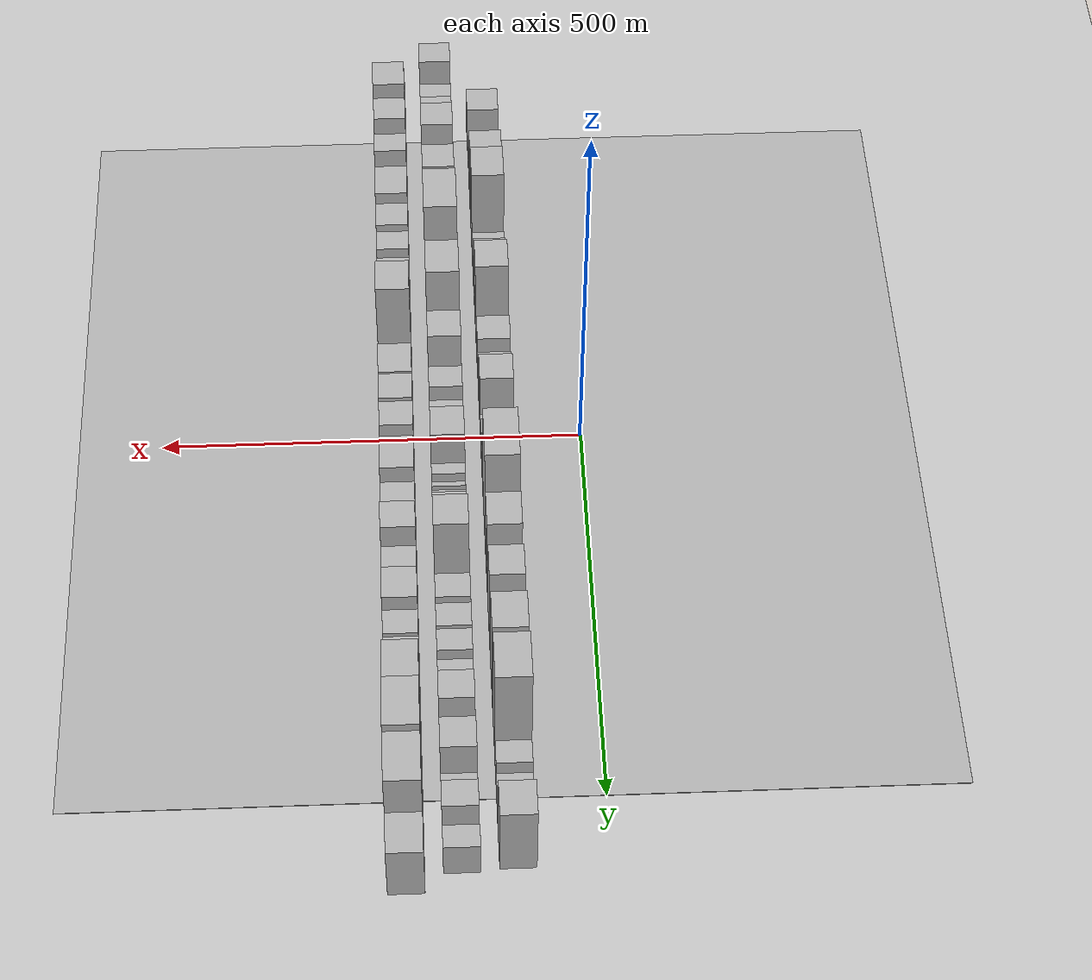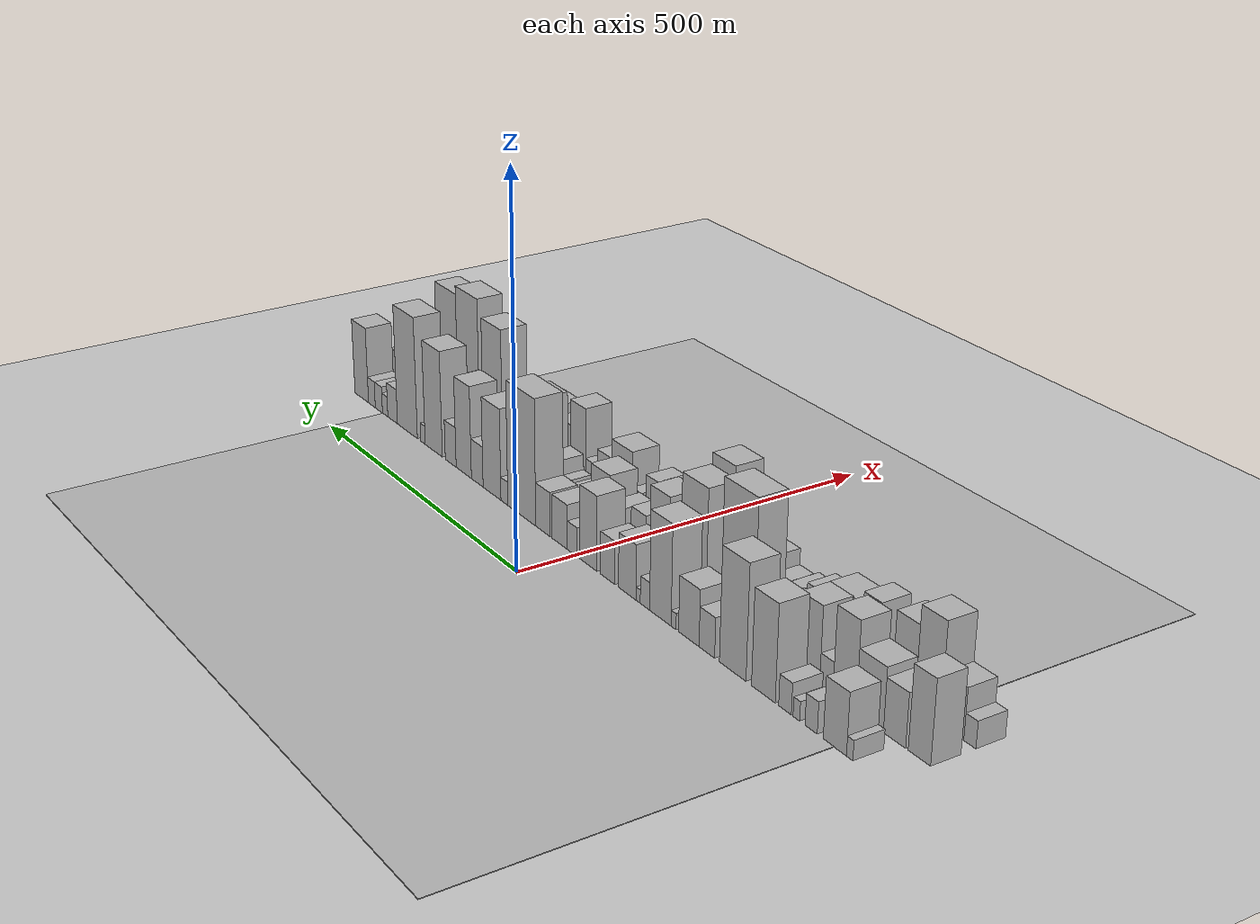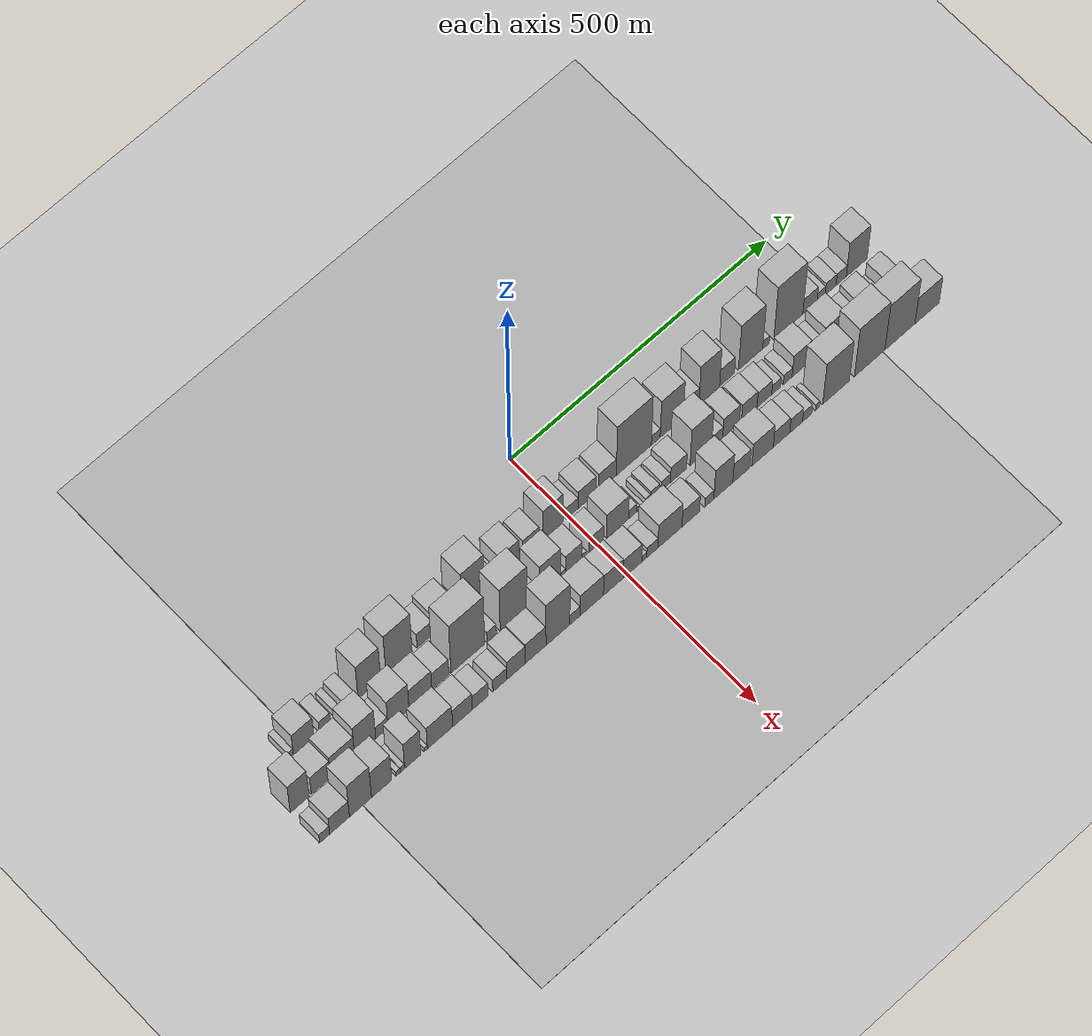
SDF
<?xml version="1.0" encoding="utf-8"?>

<sdf version="1.6">

   <world name="default">

      <gui fullscreen="0">

         <camera name="user_camera">

            <pose>-15 0 4.57585 0 0 0</pose>

            <view_controller>orbit</view_controller>

         </camera>

      </gui>

      <scene>

         <sky>

           <clouds>

             <speed>12</speed>

           </clouds>

         </sky>

         <ambient>0.4 0.4 0.4 1</ambient>

         <background>0.7 0.7 0.7 1</background>

         <shadows>1</shadows>

      </scene>

      <gravity>0 0 -9.8066</gravity>

      <magnetic_field>6e-06 2.3e-05 -4.2e-05</magnetic_field>

      <physics default="0" name="default_physics" type="ode">

         <ode>

            <solver>

               <type>quick</type>

               <iters>10</iters>

               <sor>1.0</sor>

               <use_dynamic_moi_rescaling>0</use_dynamic_moi_rescaling>

            </solver>

            <constraints>

               <cfm>0</cfm>

               <erp>0.2</erp>

               <contact_max_correcting_vel>100</contact_max_correcting_vel>

               <contact_surface_layer>0.001</contact_surface_layer>

            </constraints>

         </ode>

         <max_step_size>0.004</max_step_size>

         <real_time_factor>1</real_time_factor>

         <real_time_update_rate>250</real_time_update_rate>

      </physics>

      <light name="sun" type="directional">

         <cast_shadows>1</cast_shadows>

         <pose>0 0 10 0 0 0</pose>

         <diffuse>0.8 0.8 0.8 1</diffuse>

         <specular>0.2 0.2 0.2 1</specular>

         <attenuation>

            <range>1000</range>

            <constant>0.9</constant>

            <linear>0.01</linear>

            <quadratic>0.001</quadratic>

         </attenuation>

         <direction>-0.5 0.1 -0.9</direction>

      </light>

      <include>

         <name>ground_plane_1</name>

         <uri>model://HANNAS_ground_plane</uri>

         <pose>0 0 0  0 0 0</pose>

      </include>

      <include>

         <name>ground_plane_2</name>

         <uri>model://HANNAS_ground_plane</uri>

         <pose>100 0 0  0 0 0</pose>

      </include>

      <model name="building_1">

         <static>1</static>

         <pose frame="">100.0000 -525.4028 0 0.000000 0.000000 0.000000</pose>

         <link name="link">

            <pose frame="">0 0 12.00 0 0 0</pose>

            <collision name="collision">

               <geometry>

                  <box>

                     <size>40.0000 10.3981 24.0000</size>

                  </box>

               </geometry>

               <max_contacts>10</max_contacts>

               <surface>

                  <contact>

                     <ode/>

                  </contact>

                  <bounce/>

                  <friction>

                     <torsional>

                        <ode/>

                     </torsional>

                     <ode/>

                  </friction>

               </surface>

            </collision>

            <visual name="visual">

               <cast_shadows>0</cast_shadows>

               <geometry>

                  <box>

                     <size>40.0000 10.3981 24.0000</size>

                  </box>

               </geometry>

               <material>

                  <script>

                     <uri>model://HANNAS_wall/materials/scripts</uri>

                     <uri>model://HANNAS_wall/materials/textures</uri>

                     <name>vrc/HANNAS_wall</name>

                  </script>

               </material>

            </visual>

            <self_collide>0</self_collide>

            <enable_wind>0</enable_wind>

            <kinematic>0</kinematic>

         </link>

      </model>

      <model name="building_2">

         <static>1</static>

         <pose frame="">100.0000 -501.1264 0 0.000000 0.000000 0.000000</pose>

         <link name="link">

            <pose frame="">0 0 37.50 0 0 0</pose>

            <collision name="collision">

               <geometry>

                  <box>

                     <size>40.0000 38.1547 75.0000</size>

                  </box>

               </geometry>

               <max_contacts>10</max_contacts>

               <surface>

                  <contact>

                     <ode/>

                  </contact>

                  <bounce/>

                  <friction>

                     <torsional>

                        <ode/>

                     </torsional>

                     <ode/>

                  </friction>

               </surface>

            </collision>

            <visual name="visual">

               <cast_shadows>0</cast_shadows>

               <geometry>

                  <box>

                     <size>40.0000 38.1547 75.0000</size>

                  </box>

               </geometry>

               <material>

                  <script>

                     <uri>model://HANNAS_wall/materials/scripts</uri>

                     <uri>model://HANNAS_wall/materials/textures</uri>

                     <name>vrc/HANNAS_wall</name>

                  </script>

               </material>

            </visual>

            <self_collide>0</self_collide>

            <enable_wind>0</enable_wind>

            <kinematic>0</kinematic>

         </link>

      </model>

      <model name="building_3">

         <static>1</static>

         <pose frame="">100.0000 -461.7086 0 0.000000 0.000000 0.000000</pose>

         <link name="link">

            <pose frame="">0 0 19.50 0 0 0</pose>

            <collision name="collision">

               <geometry>

                  <box>

                     <size>40.0000 20.6809 39.0000</size>

                  </box>

               </geometry>

               <max_contacts>10</max_contacts>

               <surface>

                  <contact>

                     <ode/>

                  </contact>

                  <bounce/>

                  <friction>

                     <torsional>

                        <ode/>

                     </torsional>

                     <ode/>

                  </friction>

               </surface>

            </collision>

            <visual name="visual">

               <cast_shadows>0</cast_shadows>

               <geometry>

                  <box>

                     <size>40.0000 20.6809 39.0000</size>

                  </box>

               </geometry>

               <material>

                  <script>

                     <uri>model://HANNAS_wall/materials/scripts</uri>

                     <uri>model://HANNAS_wall/materials/textures</uri>

                     <name>vrc/HANNAS_wall</name>

                  </script>

               </material>

            </visual>

            <self_collide>0</self_collide>

            <enable_wind>0</enable_wind>

            <kinematic>0</kinematic>

         </link>

      </model>

      <model name="building_4">

         <static>1</static>

         <pose frame="">100.0000 -436.6622 0 0.000000 0.000000 0.000000</pose>

         <link name="link">

            <pose frame="">0 0 12.00 0 0 0</pose>

            <collision name="collision">

               <geometry>

                  <box>

                     <size>40.0000 11.4119 24.0000</size>

                  </box>

               </geometry>

               <max_contacts>10</max_contacts>

               <surface>

                  <contact>

                     <ode/>

                  </contact>

                  <bounce/>

                  <friction>

                     <torsional>

                        <ode/>

                     </torsional>

                     <ode/>

                  </friction>

               </surface>

            </collision>

            <visual name="visual">

               <cast_shadows>0</cast_shadows>

               <geometry>

                  <box>

                     <size>40.0000 11.4119 24.0000</size>

                  </box>

               </geometry>

               <material>

                  <script>

                     <uri>model://HANNAS_wall/materials/scripts</uri>

                     <uri>model://HANNAS_wall/materials/textures</uri>

                     <name>vrc/HANNAS_wall</name>

                  </script>

               </material>

            </visual>

            <self_collide>0</self_collide>

            <enable_wind>0</enable_wind>

            <kinematic>0</kinematic>

         </link>

      </model>

      <model name="building_5">

         <static>1</static>

         <pose frame="">100.0000 -416.9289 0 0.000000 0.000000 0.000000</pose>

         <link name="link">

            <pose frame="">0 0 19.50 0 0 0</pose>

            <collision name="collision">

               <geometry>

                  <box>

                     <size>40.0000 22.0547 39.0000</size>

                  </box>

               </geometry>

               <max_contacts>10</max_contacts>

               <surface>

                  <contact>

                     <ode/>

                  </contact>

                  <bounce/>

                  <friction>

                     <torsional>

                        <ode/>

                     </torsional>

                     <ode/>

                  </friction>

               </surface>

            </collision>

            <visual name="visual">

               <cast_shadows>0</cast_shadows>

               <geometry>

                  <box>

                     <size>40.0000 22.0547 39.0000</size>

                  </box>

               </geometry>

               <material>

                  <script>

                     <uri>model://HANNAS_wall/materials/scripts</uri>

                     <uri>model://HANNAS_wall/materials/textures</uri>

                     <name>vrc/HANNAS_wall</name>

                  </script>

               </material>

            </visual>

            <self_collide>0</self_collide>

            <enable_wind>0</enable_wind>

            <kinematic>0</kinematic>

         </link>

      </model>

      <model name="building_6">

         <static>1</static>

         <pose frame="">100.0000 -378.7087 0 0.000000 0.000000 0.000000</pose>

         <link name="link">

            <pose frame="">0 0 60.00 0 0 0</pose>

            <collision name="collision">

               <geometry>

                  <box>

                     <size>40.0000 42.3856 120.0000</size>

                  </box>

               </geometry>

               <max_contacts>10</max_contacts>

               <surface>

                  <contact>

                     <ode/>

                  </contact>

                  <bounce/>

                  <friction>

                     <torsional>

                        <ode/>

                     </torsional>

                     <ode/>

                  </friction>

               </surface>

            </collision>

            <visual name="visual">

               <cast_shadows>0</cast_shadows>

               <geometry>

                  <box>

                     <size>40.0000 42.3856 120.0000</size>

                  </box>

               </geometry>

               <material>

                  <script>

                     <uri>model://HANNAS_wall/materials/scripts</uri>

                     <uri>model://HANNAS_wall/materials/textures</uri>

                     <name>vrc/HANNAS_wall</name>

                  </script>

               </material>

            </visual>

            <self_collide>0</self_collide>

            <enable_wind>0</enable_wind>

            <kinematic>0</kinematic>

         </link>

      </model>

      <model name="building_7">

         <static>1</static>

         <pose frame="">100.0000 -322.8838 0 0.000000 0.000000 0.000000</pose>

         <link name="link">

            <pose frame="">0 0 72.00 0 0 0</pose>

            <collision name="collision">

               <geometry>

                  <box>

                     <size>40.0000 49.2643 144.0000</size>

                  </box>

               </geometry>

               <max_contacts>10</max_contacts>

               <surface>

                  <contact>

                     <ode/>

                  </contact>

                  <bounce/>

                  <friction>

                     <torsional>

                        <ode/>

                     </torsional>

                     <ode/>

                  </friction>

               </surface>

            </collision>

            <visual name="visual">

               <cast_shadows>0</cast_shadows>

               <geometry>

                  <box>

                     <size>40.0000 49.2643 144.0000</size>

                  </box>

               </geometry>

               <material>

                  <script>

                     <uri>model://HANNAS_wall/materials/scripts</uri>

                     <uri>model://HANNAS_wall/materials/textures</uri>

                     <name>vrc/HANNAS_wall</name>

                  </script>

               </material>

            </visual>

            <self_collide>0</self_collide>

            <enable_wind>0</enable_wind>

            <kinematic>0</kinematic>

         </link>

      </model>

      <model name="building_8">

         <static>1</static>

         <pose frame="">100.0000 -274.3842 0 0.000000 0.000000 0.000000</pose>

         <link name="link">

            <pose frame="">0 0 25.50 0 0 0</pose>

            <collision name="collision">

               <geometry>

                  <box>

                     <size>40.0000 29.7349 51.0000</size>

                  </box>

               </geometry>

               <max_contacts>10</max_contacts>

               <surface>

                  <contact>

                     <ode/>

                  </contact>

                  <bounce/>

                  <friction>

                     <torsional>

                        <ode/>

                     </torsional>

                     <ode/>

                  </friction>

               </surface>

            </collision>

            <visual name="visual">

               <cast_shadows>0</cast_shadows>

               <geometry>

                  <box>

                     <size>40.0000 29.7349 51.0000</size>

                  </box>

               </geometry>

               <material>

                  <script>

                     <uri>model://HANNAS_wall/materials/scripts</uri>

                     <uri>model://HANNAS_wall/materials/textures</uri>

                     <name>vrc/HANNAS_wall</name>

                  </script>

               </material>

            </visual>

            <self_collide>0</self_collide>

            <enable_wind>0</enable_wind>

            <kinematic>0</kinematic>

         </link>

      </model>

      <model name="building_9">

         <static>1</static>

         <pose frame="">100.0000 -239.4780 0 0.000000 0.000000 0.000000</pose>

         <link name="link">

            <pose frame="">0 0 36.00 0 0 0</pose>

            <collision name="collision">

               <geometry>

                  <box>

                     <size>40.0000 40.0774 72.0000</size>

                  </box>

               </geometry>

               <max_contacts>10</max_contacts>

               <surface>

                  <contact>

                     <ode/>

                  </contact>

                  <bounce/>

                  <friction>

                     <torsional>

                        <ode/>

                     </torsional>

                     <ode/>

                  </friction>

               </surface>

            </collision>

            <visual name="visual">

               <cast_shadows>0</cast_shadows>

               <geometry>

                  <box>

                     <size>40.0000 40.0774 72.0000</size>

                  </box>

               </geometry>

               <material>

                  <script>

                     <uri>model://HANNAS_wall/materials/scripts</uri>

                     <uri>model://HANNAS_wall/materials/textures</uri>

                     <name>vrc/HANNAS_wall</name>

                  </script>

               </material>

            </visual>

            <self_collide>0</self_collide>

            <enable_wind>0</enable_wind>

            <kinematic>0</kinematic>

         </link>

      </model>

      <model name="building_10">

         <static>1</static>

         <pose frame="">100.0000 -209.4909 0 0.000000 0.000000 0.000000</pose>

         <link name="link">

            <pose frame="">0 0 10.50 0 0 0</pose>

            <collision name="collision">

               <geometry>

                  <box>

                     <size>40.0000 9.8969 21.0000</size>

                  </box>

               </geometry>

               <max_contacts>10</max_contacts>

               <surface>

                  <contact>

                     <ode/>

                  </contact>

                  <bounce/>

                  <friction>

                     <torsional>

                        <ode/>

                     </torsional>

                     <ode/>

                  </friction>

               </surface>

            </collision>

            <visual name="visual">

               <cast_shadows>0</cast_shadows>

               <geometry>

                  <box>

                     <size>40.0000 9.8969 21.0000</size>

                  </box>

               </geometry>

               <material>

                  <script>

                     <uri>model://HANNAS_wall/materials/scripts</uri>

                     <uri>model://HANNAS_wall/materials/textures</uri>

                     <name>vrc/HANNAS_wall</name>

                  </script>

               </material>

            </visual>

            <self_collide>0</self_collide>

            <enable_wind>0</enable_wind>

            <kinematic>0</kinematic>

         </link>

      </model>

      <model name="building_11">

         <static>1</static>

         <pose frame="">100.0000 -182.8452 0 0.000000 0.000000 0.000000</pose>

         <link name="link">

            <pose frame="">0 0 64.50 0 0 0</pose>

            <collision name="collision">

               <geometry>

                  <box>

                     <size>40.0000 43.3944 129.0000</size>

                  </box>

               </geometry>

               <max_contacts>10</max_contacts>

               <surface>

                  <contact>

                     <ode/>

                  </contact>

                  <bounce/>

                  <friction>

                     <torsional>

                        <ode/>

                     </torsional>

                     <ode/>

                  </friction>

               </surface>

            </collision>

            <visual name="visual">

               <cast_shadows>0</cast_shadows>

               <geometry>

                  <box>

                     <size>40.0000 43.3944 129.0000</size>

                  </box>

               </geometry>

               <material>

                  <script>

                     <uri>model://HANNAS_wall/materials/scripts</uri>

                     <uri>model://HANNAS_wall/materials/textures</uri>

                     <name>vrc/HANNAS_wall</name>

                  </script>

               </material>

            </visual>

            <self_collide>0</self_collide>

            <enable_wind>0</enable_wind>

            <kinematic>0</kinematic>

         </link>

      </model>

      <model name="building_12">

         <static>1</static>

         <pose frame="">100.0000 -151.3688 0 0.000000 0.000000 0.000000</pose>

         <link name="link">

            <pose frame="">0 0 18.00 0 0 0</pose>

            <collision name="collision">

               <geometry>

                  <box>

                     <size>40.0000 19.5585 36.0000</size>

                  </box>

               </geometry>

               <max_contacts>10</max_contacts>

               <surface>

                  <contact>

                     <ode/>

                  </contact>

                  <bounce/>

                  <friction>

                     <torsional>

                        <ode/>

                     </torsional>

                     <ode/>

                  </friction>

               </surface>

            </collision>

            <visual name="visual">

               <cast_shadows>0</cast_shadows>

               <geometry>

                  <box>

                     <size>40.0000 19.5585 36.0000</size>

                  </box>

               </geometry>

               <material>

                  <script>

                     <uri>model://HANNAS_wall/materials/scripts</uri>

                     <uri>model://HANNAS_wall/materials/textures</uri>

                     <name>vrc/HANNAS_wall</name>

                  </script>

               </material>

            </visual>

            <self_collide>0</self_collide>

            <enable_wind>0</enable_wind>

            <kinematic>0</kinematic>

         </link>

      </model>

      <model name="building_13">

         <static>1</static>

         <pose frame="">100.0000 -137.1788 0 0.000000 0.000000 0.000000</pose>

         <link name="link">

            <pose frame="">0 0 9.00 0 0 0</pose>

            <collision name="collision">

               <geometry>

                  <box>

                     <size>40.0000 8.8215 18.0000</size>

                  </box>

               </geometry>

               <max_contacts>10</max_contacts>

               <surface>

                  <contact>

                     <ode/>

                  </contact>

                  <bounce/>

                  <friction>

                     <torsional>

                        <ode/>

                     </torsional>

                     <ode/>

                  </friction>

               </surface>

            </collision>

            <visual name="visual">

               <cast_shadows>0</cast_shadows>

               <geometry>

                  <box>

                     <size>40.0000 8.8215 18.0000</size>

                  </box>

               </geometry>

               <material>

                  <script>

                     <uri>model://HANNAS_wall/materials/scripts</uri>

                     <uri>model://HANNAS_wall/materials/textures</uri>

                     <name>vrc/HANNAS_wall</name>

                  </script>

               </material>

            </visual>

            <self_collide>0</self_collide>

            <enable_wind>0</enable_wind>

            <kinematic>0</kinematic>

         </link>

      </model>

      <model name="building_14">

         <static>1</static>

         <pose frame="">100.0000 -114.2665 0 0.000000 0.000000 0.000000</pose>

         <link name="link">

            <pose frame="">0 0 36.00 0 0 0</pose>

            <collision name="collision">

               <geometry>

                  <box>

                     <size>40.0000 37.0031 72.0000</size>

                  </box>

               </geometry>

               <max_contacts>10</max_contacts>

               <surface>

                  <contact>

                     <ode/>

                  </contact>

                  <bounce/>

                  <friction>

                     <torsional>

                        <ode/>

                     </torsional>

                     <ode/>

                  </friction>

               </surface>

            </collision>

            <visual name="visual">

               <cast_shadows>0</cast_shadows>

               <geometry>

                  <box>

                     <size>40.0000 37.0031 72.0000</size>

                  </box>

               </geometry>

               <material>

                  <script>

                     <uri>model://HANNAS_wall/materials/scripts</uri>

                     <uri>model://HANNAS_wall/materials/textures</uri>

                     <name>vrc/HANNAS_wall</name>

                  </script>

               </material>

            </visual>

            <self_collide>0</self_collide>

            <enable_wind>0</enable_wind>

            <kinematic>0</kinematic>

         </link>

      </model>

      <model name="building_15">

         <static>1</static>

         <pose frame="">100.0000 -72.3574 0 0.000000 0.000000 0.000000</pose>

         <link name="link">

            <pose frame="">0 0 28.50 0 0 0</pose>

            <collision name="collision">

               <geometry>

                  <box>

                     <size>40.0000 30.8151 57.0000</size>

                  </box>

               </geometry>

               <max_contacts>10</max_contacts>

               <surface>

                  <contact>

                     <ode/>

                  </contact>

                  <bounce/>

                  <friction>

                     <torsional>

                        <ode/>

                     </torsional>

                     <ode/>

                  </friction>

               </surface>

            </collision>

            <visual name="visual">

               <cast_shadows>0</cast_shadows>

               <geometry>

                  <box>

                     <size>40.0000 30.8151 57.0000</size>

                  </box>

               </geometry>

               <material>

                  <script>

                     <uri>model://HANNAS_wall/materials/scripts</uri>

                     <uri>model://HANNAS_wall/materials/textures</uri>

                     <name>vrc/HANNAS_wall</name>

                  </script>

               </material>

            </visual>

            <self_collide>0</self_collide>

            <enable_wind>0</enable_wind>

            <kinematic>0</kinematic>

         </link>

      </model>

      <model name="building_16">

         <static>1</static>

         <pose frame="">100.0000 -30.0958 0 0.000000 0.000000 0.000000</pose>

         <link name="link">

            <pose frame="">0 0 49.50 0 0 0</pose>

            <collision name="collision">

               <geometry>

                  <box>

                     <size>40.0000 37.7082 99.0000</size>

                  </box>

               </geometry>

               <max_contacts>10</max_contacts>

               <surface>

                  <contact>

                     <ode/>

                  </contact>

                  <bounce/>

                  <friction>

                     <torsional>

                        <ode/>

                     </torsional>

                     <ode/>

                  </friction>

               </surface>

            </collision>

            <visual name="visual">

               <cast_shadows>0</cast_shadows>

               <geometry>

                  <box>

                     <size>40.0000 37.7082 99.0000</size>

                  </box>

               </geometry>

               <material>

                  <script>

                     <uri>model://HANNAS_wall/materials/scripts</uri>

                     <uri>model://HANNAS_wall/materials/textures</uri>

                     <name>vrc/HANNAS_wall</name>

                  </script>

               </material>

            </visual>

            <self_collide>0</self_collide>

            <enable_wind>0</enable_wind>

            <kinematic>0</kinematic>

         </link>

      </model>

      <model name="building_17">

         <static>1</static>

         <pose frame="">100.0000 6.1590 0 0.000000 0.000000 0.000000</pose>

         <link name="link">

            <pose frame="">0 0 19.50 0 0 0</pose>

            <collision name="collision">

               <geometry>

                  <box>

                     <size>40.0000 22.8013 39.0000</size>

                  </box>

               </geometry>

               <max_contacts>10</max_contacts>

               <surface>

                  <contact>

                     <ode/>

                  </contact>

                  <bounce/>

                  <friction>

                     <torsional>

                        <ode/>

                     </torsional>

                     <ode/>

                  </friction>

               </surface>

            </collision>

            <visual name="visual">

               <cast_shadows>0</cast_shadows>

               <geometry>

                  <box>

                     <size>40.0000 22.8013 39.0000</size>

                  </box>

               </geometry>

               <material>

                  <script>

                     <uri>model://HANNAS_wall/materials/scripts</uri>

                     <uri>model://HANNAS_wall/materials/textures</uri>

                     <name>vrc/HANNAS_wall</name>

                  </script>

               </material>

            </visual>

            <self_collide>0</self_collide>

            <enable_wind>0</enable_wind>

            <kinematic>0</kinematic>

         </link>

      </model>

      <model name="building_18">

         <static>1</static>

         <pose frame="">100.0000 35.1680 0 0.000000 0.000000 0.000000</pose>

         <link name="link">

            <pose frame="">0 0 30.00 0 0 0</pose>

            <collision name="collision">

               <geometry>

                  <box>

                     <size>40.0000 35.2167 60.0000</size>

                  </box>

               </geometry>

               <max_contacts>10</max_contacts>

               <surface>

                  <contact>

                     <ode/>

                  </contact>

                  <bounce/>

                  <friction>

                     <torsional>

                        <ode/>

                     </torsional>

                     <ode/>

                  </friction>

               </surface>

            </collision>

            <visual name="visual">

               <cast_shadows>0</cast_shadows>

               <geometry>

                  <box>

                     <size>40.0000 35.2167 60.0000</size>

                  </box>

               </geometry>

               <material>

                  <script>

                     <uri>model://HANNAS_wall/materials/scripts</uri>

                     <uri>model://HANNAS_wall/materials/textures</uri>

                     <name>vrc/HANNAS_wall</name>

                  </script>

               </material>

            </visual>

            <self_collide>0</self_collide>

            <enable_wind>0</enable_wind>

            <kinematic>0</kinematic>

         </link>

      </model>

      <model name="building_19">

         <static>1</static>

         <pose frame="">100.0000 74.7181 0 0.000000 0.000000 0.000000</pose>

         <link name="link">

            <pose frame="">0 0 30.00 0 0 0</pose>

            <collision name="collision">

               <geometry>

                  <box>

                     <size>40.0000 33.8835 60.0000</size>

                  </box>

               </geometry>

               <max_contacts>10</max_contacts>

               <surface>

                  <contact>

                     <ode/>

                  </contact>

                  <bounce/>

                  <friction>

                     <torsional>

                        <ode/>

                     </torsional>

                     <ode/>

                  </friction>

               </surface>

            </collision>

            <visual name="visual">

               <cast_shadows>0</cast_shadows>

               <geometry>

                  <box>

                     <size>40.0000 33.8835 60.0000</size>

                  </box>

               </geometry>

               <material>

                  <script>

                     <uri>model://HANNAS_wall/materials/scripts</uri>

                     <uri>model://HANNAS_wall/materials/textures</uri>

                     <name>vrc/HANNAS_wall</name>

                  </script>

               </material>

            </visual>

            <self_collide>0</self_collide>

            <enable_wind>0</enable_wind>

            <kinematic>0</kinematic>

         </link>

      </model>

      <model name="building_20">

         <static>1</static>

         <pose frame="">100.0000 125.6870 0 0.000000 0.000000 0.000000</pose>

         <link name="link">

            <pose frame="">0 0 85.50 0 0 0</pose>

            <collision name="collision">

               <geometry>

                  <box>

                     <size>40.0000 68.0544 171.0000</size>

                  </box>

               </geometry>

               <max_contacts>10</max_contacts>

               <surface>

                  <contact>

                     <ode/>

                  </contact>

                  <bounce/>

                  <friction>

                     <torsional>

                        <ode/>

                     </torsional>

                     <ode/>

                  </friction>

               </surface>

            </collision>

            <visual name="visual">

               <cast_shadows>0</cast_shadows>

               <geometry>

                  <box>

                     <size>40.0000 68.0544 171.0000</size>

                  </box>

               </geometry>

               <material>

                  <script>

                     <uri>model://HANNAS_wall/materials/scripts</uri>

                     <uri>model://HANNAS_wall/materials/textures</uri>

                     <name>vrc/HANNAS_wall</name>

                  </script>

               </material>

            </visual>

            <self_collide>0</self_collide>

            <enable_wind>0</enable_wind>

            <kinematic>0</kinematic>

         </link>

      </model>

      <model name="building_21">

         <static>1</static>

         <pose frame="">100.0000 168.3000 0 0.000000 0.000000 0.000000</pose>

         <link name="link">

            <pose frame="">0 0 16.50 0 0 0</pose>

            <collision name="collision">

               <geometry>

                  <box>

                     <size>40.0000 17.1716 33.0000</size>

                  </box>

               </geometry>

               <max_contacts>10</max_contacts>

               <surface>

                  <contact>

                     <ode/>

                  </contact>

                  <bounce/>

                  <friction>

                     <torsional>

                        <ode/>

                     </torsional>

                     <ode/>

                  </friction>

               </surface>

            </collision>

            <visual name="visual">

               <cast_shadows>0</cast_shadows>

               <geometry>

                  <box>

                     <size>40.0000 17.1716 33.0000</size>

                  </box>

               </geometry>

               <material>

                  <script>

                     <uri>model://HANNAS_wall/materials/scripts</uri>

                     <uri>model://HANNAS_wall/materials/textures</uri>

                     <name>vrc/HANNAS_wall</name>

                  </script>

               </material>

            </visual>

            <self_collide>0</self_collide>

            <enable_wind>0</enable_wind>

            <kinematic>0</kinematic>

         </link>

      </model>

      <model name="building_22">

         <static>1</static>

         <pose frame="">100.0000 199.6199 0 0.000000 0.000000 0.000000</pose>

         <link name="link">

            <pose frame="">0 0 63.00 0 0 0</pose>

            <collision name="collision">

               <geometry>

                  <box>

                     <size>40.0000 45.4680 126.0000</size>

                  </box>

               </geometry>

               <max_contacts>10</max_contacts>

               <surface>

                  <contact>

                     <ode/>

                  </contact>

                  <bounce/>

                  <friction>

                     <torsional>

                        <ode/>

                     </torsional>

                     <ode/>

                  </friction>

               </surface>

            </collision>

            <visual name="visual">

               <cast_shadows>0</cast_shadows>

               <geometry>

                  <box>

                     <size>40.0000 45.4680 126.0000</size>

                  </box>

               </geometry>

               <material>

                  <script>

                     <uri>model://HANNAS_wall/materials/scripts</uri>

                     <uri>model://HANNAS_wall/materials/textures</uri>

                     <name>vrc/HANNAS_wall</name>

                  </script>

               </material>

            </visual>

            <self_collide>0</self_collide>

            <enable_wind>0</enable_wind>

            <kinematic>0</kinematic>

         </link>

      </model>

      <model name="building_23">

         <static>1</static>

         <pose frame="">100.0000 237.5084 0 0.000000 0.000000 0.000000</pose>

         <link name="link">

            <pose frame="">0 0 28.50 0 0 0</pose>

            <collision name="collision">

               <geometry>

                  <box>

                     <size>40.0000 30.3090 57.0000</size>

                  </box>

               </geometry>

               <max_contacts>10</max_contacts>

               <surface>

                  <contact>

                     <ode/>

                  </contact>

                  <bounce/>

                  <friction>

                     <torsional>

                        <ode/>

                     </torsional>

                     <ode/>

                  </friction>

               </surface>

            </collision>

            <visual name="visual">

               <cast_shadows>0</cast_shadows>

               <geometry>

                  <box>

                     <size>40.0000 30.3090 57.0000</size>

                  </box>

               </geometry>

               <material>

                  <script>

                     <uri>model://HANNAS_wall/materials/scripts</uri>

                     <uri>model://HANNAS_wall/materials/textures</uri>

                     <name>vrc/HANNAS_wall</name>

                  </script>

               </material>

            </visual>

            <self_collide>0</self_collide>

            <enable_wind>0</enable_wind>

            <kinematic>0</kinematic>

         </link>

      </model>

      <model name="building_24">

         <static>1</static>

         <pose frame="">100.0000 272.9096 0 0.000000 0.000000 0.000000</pose>

         <link name="link">

            <pose frame="">0 0 64.50 0 0 0</pose>

            <collision name="collision">

               <geometry>

                  <box>

                     <size>40.0000 40.4933 129.0000</size>

                  </box>

               </geometry>

               <max_contacts>10</max_contacts>

               <surface>

                  <contact>

                     <ode/>

                  </contact>

                  <bounce/>

                  <friction>

                     <torsional>

                        <ode/>

                     </torsional>

                     <ode/>

                  </friction>

               </surface>

            </collision>

            <visual name="visual">

               <cast_shadows>0</cast_shadows>

               <geometry>

                  <box>

                     <size>40.0000 40.4933 129.0000</size>

                  </box>

               </geometry>

               <material>

                  <script>

                     <uri>model://HANNAS_wall/materials/scripts</uri>

                     <uri>model://HANNAS_wall/materials/textures</uri>

                     <name>vrc/HANNAS_wall</name>

                  </script>

               </material>

            </visual>

            <self_collide>0</self_collide>

            <enable_wind>0</enable_wind>

            <kinematic>0</kinematic>

         </link>

      </model>

      <model name="building_25">

         <static>1</static>

         <pose frame="">100.0000 307.8030 0 0.000000 0.000000 0.000000</pose>

         <link name="link">

            <pose frame="">0 0 28.50 0 0 0</pose>

            <collision name="collision">

               <geometry>

                  <box>

                     <size>40.0000 29.2936 57.0000</size>

                  </box>

               </geometry>

               <max_contacts>10</max_contacts>

               <surface>

                  <contact>

                     <ode/>

                  </contact>

                  <bounce/>

                  <friction>

                     <torsional>

                        <ode/>

                     </torsional>

                     <ode/>

                  </friction>

               </surface>

            </collision>

            <visual name="visual">

               <cast_shadows>0</cast_shadows>

               <geometry>

                  <box>

                     <size>40.0000 29.2936 57.0000</size>

                  </box>

               </geometry>

               <material>

                  <script>

                     <uri>model://HANNAS_wall/materials/scripts</uri>

                     <uri>model://HANNAS_wall/materials/textures</uri>

                     <name>vrc/HANNAS_wall</name>

                  </script>

               </material>

            </visual>

            <self_collide>0</self_collide>

            <enable_wind>0</enable_wind>

            <kinematic>0</kinematic>

         </link>

      </model>

      <model name="building_26">

         <static>1</static>

         <pose frame="">100.0000 354.2889 0 0.000000 0.000000 0.000000</pose>

         <link name="link">

            <pose frame="">0 0 75.00 0 0 0</pose>

            <collision name="collision">

               <geometry>

                  <box>

                     <size>40.0000 47.6782 150.0000</size>

                  </box>

               </geometry>

               <max_contacts>10</max_contacts>

               <surface>

                  <contact>

                     <ode/>

                  </contact>

                  <bounce/>

                  <friction>

                     <torsional>

                        <ode/>

                     </torsional>

                     <ode/>

                  </friction>

               </surface>

            </collision>

            <visual name="visual">

               <cast_shadows>0</cast_shadows>

               <geometry>

                  <box>

                     <size>40.0000 47.6782 150.0000</size>

                  </box>

               </geometry>

               <material>

                  <script>

                     <uri>model://HANNAS_wall/materials/scripts</uri>

                     <uri>model://HANNAS_wall/materials/textures</uri>

                     <name>vrc/HANNAS_wall</name>

                  </script>

               </material>

            </visual>

            <self_collide>0</self_collide>

            <enable_wind>0</enable_wind>

            <kinematic>0</kinematic>

         </link>

      </model>

      <model name="building_27">

         <static>1</static>

         <pose frame="">100.0000 384.5869 0 0.000000 0.000000 0.000000</pose>

         <link name="link">

            <pose frame="">0 0 13.50 0 0 0</pose>

            <collision name="collision">

               <geometry>

                  <box>

                     <size>40.0000 12.9178 27.0000</size>

                  </box>

               </geometry>

               <max_contacts>10</max_contacts>

               <surface>

                  <contact>

                     <ode/>

                  </contact>

                  <bounce/>

                  <friction>

                     <torsional>

                        <ode/>

                     </torsional>

                     <ode/>

                  </friction>

               </surface>

            </collision>

            <visual name="visual">

               <cast_shadows>0</cast_shadows>

               <geometry>

                  <box>

                     <size>40.0000 12.9178 27.0000</size>

                  </box>

               </geometry>

               <material>

                  <script>

                     <uri>model://HANNAS_wall/materials/scripts</uri>

                     <uri>model://HANNAS_wall/materials/textures</uri>

                     <name>vrc/HANNAS_wall</name>

                  </script>

               </material>

            </visual>

            <self_collide>0</self_collide>

            <enable_wind>0</enable_wind>

            <kinematic>0</kinematic>

         </link>

      </model>

      <model name="building_28">

         <static>1</static>

         <pose frame="">100.0000 428.7757 0 0.000000 0.000000 0.000000</pose>

         <link name="link">

            <pose frame="">0 0 87.00 0 0 0</pose>

            <collision name="collision">

               <geometry>

                  <box>

                     <size>40.0000 57.4597 174.0000</size>

                  </box>

               </geometry>

               <max_contacts>10</max_contacts>

               <surface>

                  <contact>

                     <ode/>

                  </contact>

                  <bounce/>

                  <friction>

                     <torsional>

                        <ode/>

                     </torsional>

                     <ode/>

                  </friction>

               </surface>

            </collision>

            <visual name="visual">

               <cast_shadows>0</cast_shadows>

               <geometry>

                  <box>

                     <size>40.0000 57.4597 174.0000</size>

                  </box>

               </geometry>

               <material>

                  <script>

                     <uri>model://HANNAS_wall/materials/scripts</uri>

                     <uri>model://HANNAS_wall/materials/textures</uri>

                     <name>vrc/HANNAS_wall</name>

                  </script>

               </material>

            </visual>

            <self_collide>0</self_collide>

            <enable_wind>0</enable_wind>

            <kinematic>0</kinematic>

         </link>

      </model>

      <model name="building_29">

         <static>1</static>

         <pose frame="">100.0000 471.7689 0 0.000000 0.000000 0.000000</pose>

         <link name="link">

            <pose frame="">0 0 25.50 0 0 0</pose>

            <collision name="collision">

               <geometry>

                  <box>

                     <size>40.0000 28.5268 51.0000</size>

                  </box>

               </geometry>

               <max_contacts>10</max_contacts>

               <surface>

                  <contact>

                     <ode/>

                  </contact>

                  <bounce/>

                  <friction>

                     <torsional>

                        <ode/>

                     </torsional>

                     <ode/>

                  </friction>

               </surface>

            </collision>

            <visual name="visual">

               <cast_shadows>0</cast_shadows>

               <geometry>

                  <box>

                     <size>40.0000 28.5268 51.0000</size>

                  </box>

               </geometry>

               <material>

                  <script>

                     <uri>model://HANNAS_wall/materials/scripts</uri>

                     <uri>model://HANNAS_wall/materials/textures</uri>

                     <name>vrc/HANNAS_wall</name>

                  </script>

               </material>

            </visual>

            <self_collide>0</self_collide>

            <enable_wind>0</enable_wind>

            <kinematic>0</kinematic>

         </link>

      </model>

      <model name="building_30">

         <static>1</static>

         <pose frame="">100.0000 494.0220 0 0.000000 0.000000 0.000000</pose>

         <link name="link">

            <pose frame="">0 0 15.00 0 0 0</pose>

            <collision name="collision">

               <geometry>

                  <box>

                     <size>40.0000 15.9793 30.0000</size>

                  </box>

               </geometry>

               <max_contacts>10</max_contacts>

               <surface>

                  <contact>

                     <ode/>

                  </contact>

                  <bounce/>

                  <friction>

                     <torsional>

                        <ode/>

                     </torsional>

                     <ode/>

                  </friction>

               </surface>

            </collision>

            <visual name="visual">

               <cast_shadows>0</cast_shadows>

               <geometry>

                  <box>

                     <size>40.0000 15.9793 30.0000</size>

                  </box>

               </geometry>

               <material>

                  <script>

                     <uri>model://HANNAS_wall/materials/scripts</uri>

                     <uri>model://HANNAS_wall/materials/textures</uri>

                     <name>vrc/HANNAS_wall</name>

                  </script>

               </material>

            </visual>

            <self_collide>0</self_collide>

            <enable_wind>0</enable_wind>

            <kinematic>0</kinematic>

         </link>

      </model>

      <model name="building_31">

         <static>1</static>

         <pose frame="">100.0000 512.8624 0 0.000000 0.000000 0.000000</pose>

         <link name="link">

            <pose frame="">0 0 19.50 0 0 0</pose>

            <collision name="collision">

               <geometry>

                  <box>

                     <size>40.0000 21.7016 39.0000</size>

                  </box>

               </geometry>

               <max_contacts>10</max_contacts>

               <surface>

                  <contact>

                     <ode/>

                  </contact>

                  <bounce/>

                  <friction>

                     <torsional>

                        <ode/>

                     </torsional>

                     <ode/>

                  </friction>

               </surface>

            </collision>

            <visual name="visual">

               <cast_shadows>0</cast_shadows>

               <geometry>

                  <box>

                     <size>40.0000 21.7016 39.0000</size>

                  </box>

               </geometry>

               <material>

                  <script>

                     <uri>model://HANNAS_wall/materials/scripts</uri>

                     <uri>model://HANNAS_wall/materials/textures</uri>

                     <name>vrc/HANNAS_wall</name>

                  </script>

               </material>

            </visual>

            <self_collide>0</self_collide>

            <enable_wind>0</enable_wind>

            <kinematic>0</kinematic>

         </link>

      </model>

      <model name="building_32">

         <static>1</static>

         <pose frame="">100.0000 533.9631 0 0.000000 0.000000 0.000000</pose>

         <link name="link">

            <pose frame="">0 0 19.50 0 0 0</pose>

            <collision name="collision">

               <geometry>

                  <box>

                     <size>40.0000 20.4997 39.0000</size>

                  </box>

               </geometry>

               <max_contacts>10</max_contacts>

               <surface>

                  <contact>

                     <ode/>

                  </contact>

                  <bounce/>

                  <friction>

                     <torsional>

                        <ode/>

                     </torsional>

                     <ode/>

                  </friction>

               </surface>

            </collision>

            <visual name="visual">

               <cast_shadows>0</cast_shadows>

               <geometry>

                  <box>

                     <size>40.0000 20.4997 39.0000</size>

                  </box>

               </geometry>

               <material>

                  <script>

                     <uri>model://HANNAS_wall/materials/scripts</uri>

                     <uri>model://HANNAS_wall/materials/textures</uri>

                     <name>vrc/HANNAS_wall</name>

                  </script>

               </material>

            </visual>

            <self_collide>0</self_collide>

            <enable_wind>0</enable_wind>

            <kinematic>0</kinematic>

         </link>

      </model>

      <model name="building_33">

         <static>1</static>

         <pose frame="">100.0000 565.1274 0 0.000000 0.000000 0.000000</pose>

         <link name="link">

            <pose frame="">0 0 55.50 0 0 0</pose>

            <collision name="collision">

               <geometry>

                  <box>

                     <size>40.0000 41.8290 111.0000</size>

                  </box>

               </geometry>

               <max_contacts>10</max_contacts>

               <surface>

                  <contact>

                     <ode/>

                  </contact>

                  <bounce/>

                  <friction>

                     <torsional>

                        <ode/>

                     </torsional>

                     <ode/>

                  </friction>

               </surface>

            </collision>

            <visual name="visual">

               <cast_shadows>0</cast_shadows>

               <geometry>

                  <box>

                     <size>40.0000 41.8290 111.0000</size>

                  </box>

               </geometry>

               <material>

                  <script>

                     <uri>model://HANNAS_wall/materials/scripts</uri>

                     <uri>model://HANNAS_wall/materials/textures</uri>

                     <name>vrc/HANNAS_wall</name>

                  </script>

               </material>

            </visual>

            <self_collide>0</self_collide>

            <enable_wind>0</enable_wind>

            <kinematic>0</kinematic>

         </link>

      </model>

      <model name="building_34">

         <static>1</static>

         <pose frame="">160.0000 -562.5379 0 0.000000 0.000000 0.000000</pose>

         <link name="link">

            <pose frame="">0 0 51.00 0 0 0</pose>

            <collision name="collision">

               <geometry>

                  <box>

                     <size>40.0000 34.9241 102.0000</size>

                  </box>

               </geometry>

               <max_contacts>10</max_contacts>

               <surface>

                  <contact>

                     <ode/>

                  </contact>

                  <bounce/>

                  <friction>

                     <torsional>

                        <ode/>

                     </torsional>

                     <ode/>

                  </friction>

               </surface>

            </collision>

            <visual name="visual">

               <cast_shadows>0</cast_shadows>

               <geometry>

                  <box>

                     <size>40.0000 34.9241 102.0000</size>

                  </box>

               </geometry>

               <material>

                  <script>

                     <uri>model://HANNAS_wall/materials/scripts</uri>

                     <uri>model://HANNAS_wall/materials/textures</uri>

                     <name>vrc/HANNAS_wall</name>

                  </script>

               </material>

            </visual>

            <self_collide>0</self_collide>

            <enable_wind>0</enable_wind>

            <kinematic>0</kinematic>

         </link>

      </model>

      <model name="building_35">

         <static>1</static>

         <pose frame="">160.0000 -523.3172 0 0.000000 0.000000 0.000000</pose>

         <link name="link">

            <pose frame="">0 0 33.00 0 0 0</pose>

            <collision name="collision">

               <geometry>

                  <box>

                     <size>40.0000 35.5174 66.0000</size>

                  </box>

               </geometry>

               <max_contacts>10</max_contacts>

               <surface>

                  <contact>

                     <ode/>

                  </contact>

                  <bounce/>

                  <friction>

                     <torsional>

                        <ode/>

                     </torsional>

                     <ode/>

                  </friction>

               </surface>

            </collision>

            <visual name="visual">

               <cast_shadows>0</cast_shadows>

               <geometry>

                  <box>

                     <size>40.0000 35.5174 66.0000</size>

                  </box>

               </geometry>

               <material>

                  <script>

                     <uri>model://HANNAS_wall/materials/scripts</uri>

                     <uri>model://HANNAS_wall/materials/textures</uri>

                     <name>vrc/HANNAS_wall</name>

                  </script>

               </material>

            </visual>

            <self_collide>0</self_collide>

            <enable_wind>0</enable_wind>

            <kinematic>0</kinematic>

         </link>

      </model>

      <model name="building_36">

         <static>1</static>

         <pose frame="">160.0000 -483.0762 0 0.000000 0.000000 0.000000</pose>

         <link name="link">

            <pose frame="">0 0 39.00 0 0 0</pose>

            <collision name="collision">

               <geometry>

                  <box>

                     <size>40.0000 44.9645 78.0000</size>

                  </box>

               </geometry>

               <max_contacts>10</max_contacts>

               <surface>

                  <contact>

                     <ode/>

                  </contact>

                  <bounce/>

                  <friction>

                     <torsional>

                        <ode/>

                     </torsional>

                     <ode/>

                  </friction>

               </surface>

            </collision>

            <visual name="visual">

               <cast_shadows>0</cast_shadows>

               <geometry>

                  <box>

                     <size>40.0000 44.9645 78.0000</size>

                  </box>

               </geometry>

               <material>

                  <script>

                     <uri>model://HANNAS_wall/materials/scripts</uri>

                     <uri>model://HANNAS_wall/materials/textures</uri>

                     <name>vrc/HANNAS_wall</name>

                  </script>

               </material>

            </visual>

            <self_collide>0</self_collide>

            <enable_wind>0</enable_wind>

            <kinematic>0</kinematic>

         </link>

      </model>

      <model name="building_37">

         <static>1</static>

         <pose frame="">160.0000 -440.9841 0 0.000000 0.000000 0.000000</pose>

         <link name="link">

            <pose frame="">0 0 55.50 0 0 0</pose>

            <collision name="collision">

               <geometry>

                  <box>

                     <size>40.0000 39.2198 111.0000</size>

                  </box>

               </geometry>

               <max_contacts>10</max_contacts>

               <surface>

                  <contact>

                     <ode/>

                  </contact>

                  <bounce/>

                  <friction>

                     <torsional>

                        <ode/>

                     </torsional>

                     <ode/>

                  </friction>

               </surface>

            </collision>

            <visual name="visual">

               <cast_shadows>0</cast_shadows>

               <geometry>

                  <box>

                     <size>40.0000 39.2198 111.0000</size>

                  </box>

               </geometry>

               <material>

                  <script>

                     <uri>model://HANNAS_wall/materials/scripts</uri>

                     <uri>model://HANNAS_wall/materials/textures</uri>

                     <name>vrc/HANNAS_wall</name>

                  </script>

               </material>

            </visual>

            <self_collide>0</self_collide>

            <enable_wind>0</enable_wind>

            <kinematic>0</kinematic>

         </link>

      </model>

      <model name="building_38">

         <static>1</static>

         <pose frame="">160.0000 -409.8720 0 0.000000 0.000000 0.000000</pose>

         <link name="link">

            <pose frame="">0 0 21.00 0 0 0</pose>

            <collision name="collision">

               <geometry>

                  <box>

                     <size>40.0000 23.0044 42.0000</size>

                  </box>

               </geometry>

               <max_contacts>10</max_contacts>

               <surface>

                  <contact>

                     <ode/>

                  </contact>

                  <bounce/>

                  <friction>

                     <torsional>

                        <ode/>

                     </torsional>

                     <ode/>

                  </friction>

               </surface>

            </collision>

            <visual name="visual">

               <cast_shadows>0</cast_shadows>

               <geometry>

                  <box>

                     <size>40.0000 23.0044 42.0000</size>

                  </box>

               </geometry>

               <material>

                  <script>

                     <uri>model://HANNAS_wall/materials/scripts</uri>

                     <uri>model://HANNAS_wall/materials/textures</uri>

                     <name>vrc/HANNAS_wall</name>

                  </script>

               </material>

            </visual>

            <self_collide>0</self_collide>

            <enable_wind>0</enable_wind>

            <kinematic>0</kinematic>

         </link>

      </model>

      <model name="building_39">

         <static>1</static>

         <pose frame="">160.0000 -378.7268 0 0.000000 0.000000 0.000000</pose>

         <link name="link">

            <pose frame="">0 0 49.50 0 0 0</pose>

            <collision name="collision">

               <geometry>

                  <box>

                     <size>40.0000 39.2858 99.0000</size>

                  </box>

               </geometry>

               <max_contacts>10</max_contacts>

               <surface>

                  <contact>

                     <ode/>

                  </contact>

                  <bounce/>

                  <friction>

                     <torsional>

                        <ode/>

                     </torsional>

                     <ode/>

                  </friction>

               </surface>

            </collision>

            <visual name="visual">

               <cast_shadows>0</cast_shadows>

               <geometry>

                  <box>

                     <size>40.0000 39.2858 99.0000</size>

                  </box>

               </geometry>

               <material>

                  <script>

                     <uri>model://HANNAS_wall/materials/scripts</uri>

                     <uri>model://HANNAS_wall/materials/textures</uri>

                     <name>vrc/HANNAS_wall</name>

                  </script>

               </material>

            </visual>

            <self_collide>0</self_collide>

            <enable_wind>0</enable_wind>

            <kinematic>0</kinematic>

         </link>

      </model>

      <model name="building_40">

         <static>1</static>

         <pose frame="">160.0000 -337.7056 0 0.000000 0.000000 0.000000</pose>

         <link name="link">

            <pose frame="">0 0 36.00 0 0 0</pose>

            <collision name="collision">

               <geometry>

                  <box>

                     <size>40.0000 42.7567 72.0000</size>

                  </box>

               </geometry>

               <max_contacts>10</max_contacts>

               <surface>

                  <contact>

                     <ode/>

                  </contact>

                  <bounce/>

                  <friction>

                     <torsional>

                        <ode/>

                     </torsional>

                     <ode/>

                  </friction>

               </surface>

            </collision>

            <visual name="visual">

               <cast_shadows>0</cast_shadows>

               <geometry>

                  <box>

                     <size>40.0000 42.7567 72.0000</size>

                  </box>

               </geometry>

               <material>

                  <script>

                     <uri>model://HANNAS_wall/materials/scripts</uri>

                     <uri>model://HANNAS_wall/materials/textures</uri>

                     <name>vrc/HANNAS_wall</name>

                  </script>

               </material>

            </visual>

            <self_collide>0</self_collide>

            <enable_wind>0</enable_wind>

            <kinematic>0</kinematic>

         </link>

      </model>

      <model name="building_41">

         <static>1</static>

         <pose frame="">160.0000 -300.3167 0 0.000000 0.000000 0.000000</pose>

         <link name="link">

            <pose frame="">0 0 30.00 0 0 0</pose>

            <collision name="collision">

               <geometry>

                  <box>

                     <size>40.0000 32.0211 60.0000</size>

                  </box>

               </geometry>

               <max_contacts>10</max_contacts>

               <surface>

                  <contact>

                     <ode/>

                  </contact>

                  <bounce/>

                  <friction>

                     <torsional>

                        <ode/>

                     </torsional>

                     <ode/>

                  </friction>

               </surface>

            </collision>

            <visual name="visual">

               <cast_shadows>0</cast_shadows>

               <geometry>

                  <box>

                     <size>40.0000 32.0211 60.0000</size>

                  </box>

               </geometry>

               <material>

                  <script>

                     <uri>model://HANNAS_wall/materials/scripts</uri>

                     <uri>model://HANNAS_wall/materials/textures</uri>

                     <name>vrc/HANNAS_wall</name>

                  </script>

               </material>

            </visual>

            <self_collide>0</self_collide>

            <enable_wind>0</enable_wind>

            <kinematic>0</kinematic>

         </link>

      </model>

      <model name="building_42">

         <static>1</static>

         <pose frame="">160.0000 -248.3981 0 0.000000 0.000000 0.000000</pose>

         <link name="link">

            <pose frame="">0 0 88.50 0 0 0</pose>

            <collision name="collision">

               <geometry>

                  <box>

                     <size>40.0000 63.8161 177.0000</size>

                  </box>

               </geometry>

               <max_contacts>10</max_contacts>

               <surface>

                  <contact>

                     <ode/>

                  </contact>

                  <bounce/>

                  <friction>

                     <torsional>

                        <ode/>

                     </torsional>

                     <ode/>

                  </friction>

               </surface>

            </collision>

            <visual name="visual">

               <cast_shadows>0</cast_shadows>

               <geometry>

                  <box>

                     <size>40.0000 63.8161 177.0000</size>

                  </box>

               </geometry>

               <material>

                  <script>

                     <uri>model://HANNAS_wall/materials/scripts</uri>

                     <uri>model://HANNAS_wall/materials/textures</uri>

                     <name>vrc/HANNAS_wall</name>

                  </script>

               </material>

            </visual>

            <self_collide>0</self_collide>

            <enable_wind>0</enable_wind>

            <kinematic>0</kinematic>

         </link>

      </model>

      <model name="building_43">

         <static>1</static>

         <pose frame="">160.0000 -203.3899 0 0.000000 0.000000 0.000000</pose>

         <link name="link">

            <pose frame="">0 0 18.00 0 0 0</pose>

            <collision name="collision">

               <geometry>

                  <box>

                     <size>40.0000 18.2003 36.0000</size>

                  </box>

               </geometry>

               <max_contacts>10</max_contacts>

               <surface>

                  <contact>

                     <ode/>

                  </contact>

                  <bounce/>

                  <friction>

                     <torsional>

                        <ode/>

                     </torsional>

                     <ode/>

                  </friction>

               </surface>

            </collision>

            <visual name="visual">

               <cast_shadows>0</cast_shadows>

               <geometry>

                  <box>

                     <size>40.0000 18.2003 36.0000</size>

                  </box>

               </geometry>

               <material>

                  <script>

                     <uri>model://HANNAS_wall/materials/scripts</uri>

                     <uri>model://HANNAS_wall/materials/textures</uri>

                     <name>vrc/HANNAS_wall</name>

                  </script>

               </material>

            </visual>

            <self_collide>0</self_collide>

            <enable_wind>0</enable_wind>

            <kinematic>0</kinematic>

         </link>

      </model>

      <model name="building_44">

         <static>1</static>

         <pose frame="">160.0000 -161.5203 0 0.000000 0.000000 0.000000</pose>

         <link name="link">

            <pose frame="">0 0 75.00 0 0 0</pose>

            <collision name="collision">

               <geometry>

                  <box>

                     <size>40.0000 51.5389 150.0000</size>

                  </box>

               </geometry>

               <max_contacts>10</max_contacts>

               <surface>

                  <contact>

                     <ode/>

                  </contact>

                  <bounce/>

                  <friction>

                     <torsional>

                        <ode/>

                     </torsional>

                     <ode/>

                  </friction>

               </surface>

            </collision>

            <visual name="visual">

               <cast_shadows>0</cast_shadows>

               <geometry>

                  <box>

                     <size>40.0000 51.5389 150.0000</size>

                  </box>

               </geometry>

               <material>

                  <script>

                     <uri>model://HANNAS_wall/materials/scripts</uri>

                     <uri>model://HANNAS_wall/materials/textures</uri>

                     <name>vrc/HANNAS_wall</name>

                  </script>

               </material>

            </visual>

            <self_collide>0</self_collide>

            <enable_wind>0</enable_wind>

            <kinematic>0</kinematic>

         </link>

      </model>

      <model name="building_45">

         <static>1</static>

         <pose frame="">160.0000 -120.8886 0 0.000000 0.000000 0.000000</pose>

         <link name="link">

            <pose frame="">0 0 16.50 0 0 0</pose>

            <collision name="collision">

               <geometry>

                  <box>

                     <size>40.0000 17.7243 33.0000</size>

                  </box>

               </geometry>

               <max_contacts>10</max_contacts>

               <surface>

                  <contact>

                     <ode/>

                  </contact>

                  <bounce/>

                  <friction>

                     <torsional>

                        <ode/>

                     </torsional>

                     <ode/>

                  </friction>

               </surface>

            </collision>

            <visual name="visual">

               <cast_shadows>0</cast_shadows>

               <geometry>

                  <box>

                     <size>40.0000 17.7243 33.0000</size>

                  </box>

               </geometry>

               <material>

                  <script>

                     <uri>model://HANNAS_wall/materials/scripts</uri>

                     <uri>model://HANNAS_wall/materials/textures</uri>

                     <name>vrc/HANNAS_wall</name>

                  </script>

               </material>

            </visual>

            <self_collide>0</self_collide>

            <enable_wind>0</enable_wind>

            <kinematic>0</kinematic>

         </link>

      </model>

      <model name="building_46">

         <static>1</static>

         <pose frame="">160.0000 -91.6735 0 0.000000 0.000000 0.000000</pose>

         <link name="link">

            <pose frame="">0 0 54.00 0 0 0</pose>

            <collision name="collision">

               <geometry>

                  <box>

                     <size>40.0000 40.7060 108.0000</size>

                  </box>

               </geometry>

               <max_contacts>10</max_contacts>

               <surface>

                  <contact>

                     <ode/>

                  </contact>

                  <bounce/>

                  <friction>

                     <torsional>

                        <ode/>

                     </torsional>

                     <ode/>

                  </friction>

               </surface>

            </collision>

            <visual name="visual">

               <cast_shadows>0</cast_shadows>

               <geometry>

                  <box>

                     <size>40.0000 40.7060 108.0000</size>

                  </box>

               </geometry>

               <material>

                  <script>

                     <uri>model://HANNAS_wall/materials/scripts</uri>

                     <uri>model://HANNAS_wall/materials/textures</uri>

                     <name>vrc/HANNAS_wall</name>

                  </script>

               </material>

            </visual>

            <self_collide>0</self_collide>

            <enable_wind>0</enable_wind>

            <kinematic>0</kinematic>

         </link>

      </model>

      <model name="building_47">

         <static>1</static>

         <pose frame="">160.0000 -66.9246 0 0.000000 0.000000 0.000000</pose>

         <link name="link">

            <pose frame="">0 0 9.00 0 0 0</pose>

            <collision name="collision">

               <geometry>

                  <box>

                     <size>40.0000 8.7919 18.0000</size>

                  </box>

               </geometry>

               <max_contacts>10</max_contacts>

               <surface>

                  <contact>

                     <ode/>

                  </contact>

                  <bounce/>

                  <friction>

                     <torsional>

                        <ode/>

                     </torsional>

                     <ode/>

                  </friction>

               </surface>

            </collision>

            <visual name="visual">

               <cast_shadows>0</cast_shadows>

               <geometry>

                  <box>

                     <size>40.0000 8.7919 18.0000</size>

                  </box>

               </geometry>

               <material>

                  <script>

                     <uri>model://HANNAS_wall/materials/scripts</uri>

                     <uri>model://HANNAS_wall/materials/textures</uri>

                     <name>vrc/HANNAS_wall</name>

                  </script>

               </material>

            </visual>

            <self_collide>0</self_collide>

            <enable_wind>0</enable_wind>

            <kinematic>0</kinematic>

         </link>

      </model>

      <model name="building_48">

         <static>1</static>

         <pose frame="">160.0000 -46.6002 0 0.000000 0.000000 0.000000</pose>

         <link name="link">

            <pose frame="">0 0 31.50 0 0 0</pose>

            <collision name="collision">

               <geometry>

                  <box>

                     <size>40.0000 31.8569 63.0000</size>

                  </box>

               </geometry>

               <max_contacts>10</max_contacts>

               <surface>

                  <contact>

                     <ode/>

                  </contact>

                  <bounce/>

                  <friction>

                     <torsional>

                        <ode/>

                     </torsional>

                     <ode/>

                  </friction>

               </surface>

            </collision>

            <visual name="visual">

               <cast_shadows>0</cast_shadows>

               <geometry>

                  <box>

                     <size>40.0000 31.8569 63.0000</size>

                  </box>

               </geometry>

               <material>

                  <script>

                     <uri>model://HANNAS_wall/materials/scripts</uri>

                     <uri>model://HANNAS_wall/materials/textures</uri>

                     <name>vrc/HANNAS_wall</name>

                  </script>

               </material>

            </visual>

            <self_collide>0</self_collide>

            <enable_wind>0</enable_wind>

            <kinematic>0</kinematic>

         </link>

      </model>

      <model name="building_49">

         <static>1</static>

         <pose frame="">160.0000 -26.6145 0 0.000000 0.000000 0.000000</pose>

         <link name="link">

            <pose frame="">0 0 9.00 0 0 0</pose>

            <collision name="collision">

               <geometry>

                  <box>

                     <size>40.0000 8.1146 18.0000</size>

                  </box>

               </geometry>

               <max_contacts>10</max_contacts>

               <surface>

                  <contact>

                     <ode/>

                  </contact>

                  <bounce/>

                  <friction>

                     <torsional>

                        <ode/>

                     </torsional>

                     <ode/>

                  </friction>

               </surface>

            </collision>

            <visual name="visual">

               <cast_shadows>0</cast_shadows>

               <geometry>

                  <box>

                     <size>40.0000 8.1146 18.0000</size>

                  </box>

               </geometry>

               <material>

                  <script>

                     <uri>model://HANNAS_wall/materials/scripts</uri>

                     <uri>model://HANNAS_wall/materials/textures</uri>

                     <name>vrc/HANNAS_wall</name>

                  </script>

               </material>

            </visual>

            <self_collide>0</self_collide>

            <enable_wind>0</enable_wind>

            <kinematic>0</kinematic>

         </link>

      </model>

      <model name="building_50">

         <static>1</static>

         <pose frame="">160.0000 -3.5424 0 0.000000 0.000000 0.000000</pose>

         <link name="link">

            <pose frame="">0 0 27.00 0 0 0</pose>

            <collision name="collision">

               <geometry>

                  <box>

                     <size>40.0000 28.0295 54.0000</size>

                  </box>

               </geometry>

               <max_contacts>10</max_contacts>

               <surface>

                  <contact>

                     <ode/>

                  </contact>

                  <bounce/>

                  <friction>

                     <torsional>

                        <ode/>

                     </torsional>

                     <ode/>

                  </friction>

               </surface>

            </collision>

            <visual name="visual">

               <cast_shadows>0</cast_shadows>

               <geometry>

                  <box>

                     <size>40.0000 28.0295 54.0000</size>

                  </box>

               </geometry>

               <material>

                  <script>

                     <uri>model://HANNAS_wall/materials/scripts</uri>

                     <uri>model://HANNAS_wall/materials/textures</uri>

                     <name>vrc/HANNAS_wall</name>

                  </script>

               </material>

            </visual>

            <self_collide>0</self_collide>

            <enable_wind>0</enable_wind>

            <kinematic>0</kinematic>

         </link>

      </model>

      <model name="building_51">

         <static>1</static>

         <pose frame="">160.0000 37.7399 0 0.000000 0.000000 0.000000</pose>

         <link name="link">

            <pose frame="">0 0 42.00 0 0 0</pose>

            <collision name="collision">

               <geometry>

                  <box>

                     <size>40.0000 42.5352 84.0000</size>

                  </box>

               </geometry>

               <max_contacts>10</max_contacts>

               <surface>

                  <contact>

                     <ode/>

                  </contact>

                  <bounce/>

                  <friction>

                     <torsional>

                        <ode/>

                     </torsional>

                     <ode/>

                  </friction>

               </surface>

            </collision>

            <visual name="visual">

               <cast_shadows>0</cast_shadows>

               <geometry>

                  <box>

                     <size>40.0000 42.5352 84.0000</size>

                  </box>

               </geometry>

               <material>

                  <script>

                     <uri>model://HANNAS_wall/materials/scripts</uri>

                     <uri>model://HANNAS_wall/materials/textures</uri>

                     <name>vrc/HANNAS_wall</name>

                  </script>

               </material>

            </visual>

            <self_collide>0</self_collide>

            <enable_wind>0</enable_wind>

            <kinematic>0</kinematic>

         </link>

      </model>

      <model name="building_52">

         <static>1</static>

         <pose frame="">160.0000 66.9542 0 0.000000 0.000000 0.000000</pose>

         <link name="link">

            <pose frame="">0 0 15.00 0 0 0</pose>

            <collision name="collision">

               <geometry>

                  <box>

                     <size>40.0000 15.8933 30.0000</size>

                  </box>

               </geometry>

               <max_contacts>10</max_contacts>

               <surface>

                  <contact>

                     <ode/>

                  </contact>

                  <bounce/>

                  <friction>

                     <torsional>

                        <ode/>

                     </torsional>

                     <ode/>

                  </friction>

               </surface>

            </collision>

            <visual name="visual">

               <cast_shadows>0</cast_shadows>

               <geometry>

                  <box>

                     <size>40.0000 15.8933 30.0000</size>

                  </box>

               </geometry>

               <material>

                  <script>

                     <uri>model://HANNAS_wall/materials/scripts</uri>

                     <uri>model://HANNAS_wall/materials/textures</uri>

                     <name>vrc/HANNAS_wall</name>

                  </script>

               </material>

            </visual>

            <self_collide>0</self_collide>

            <enable_wind>0</enable_wind>

            <kinematic>0</kinematic>

         </link>

      </model>

      <model name="building_53">

         <static>1</static>

         <pose frame="">160.0000 78.2024 0 0.000000 0.000000 0.000000</pose>

         <link name="link">

            <pose frame="">0 0 7.50 0 0 0</pose>

            <collision name="collision">

               <geometry>

                  <box>

                     <size>40.0000 6.6032 15.0000</size>

                  </box>

               </geometry>

               <max_contacts>10</max_contacts>

               <surface>

                  <contact>

                     <ode/>

                  </contact>

                  <bounce/>

                  <friction>

                     <torsional>

                        <ode/>

                     </torsional>

                     <ode/>

                  </friction>

               </surface>

            </collision>

            <visual name="visual">

               <cast_shadows>0</cast_shadows>

               <geometry>

                  <box>

                     <size>40.0000 6.6032 15.0000</size>

                  </box>

               </geometry>

               <material>

                  <script>

                     <uri>model://HANNAS_wall/materials/scripts</uri>

                     <uri>model://HANNAS_wall/materials/textures</uri>

                     <name>vrc/HANNAS_wall</name>

                  </script>

               </material>

            </visual>

            <self_collide>0</self_collide>

            <enable_wind>0</enable_wind>

            <kinematic>0</kinematic>

         </link>

      </model>

      <model name="building_54">

         <static>1</static>

         <pose frame="">160.0000 96.3459 0 0.000000 0.000000 0.000000</pose>

         <link name="link">

            <pose frame="">0 0 10.50 0 0 0</pose>

            <collision name="collision">

               <geometry>

                  <box>

                     <size>40.0000 9.6839 21.0000</size>

                  </box>

               </geometry>

               <max_contacts>10</max_contacts>

               <surface>

                  <contact>

                     <ode/>

                  </contact>

                  <bounce/>

                  <friction>

                     <torsional>

                        <ode/>

                     </torsional>

                     <ode/>

                  </friction>

               </surface>

            </collision>

            <visual name="visual">

               <cast_shadows>0</cast_shadows>

               <geometry>

                  <box>

                     <size>40.0000 9.6839 21.0000</size>

                  </box>

               </geometry>

               <material>

                  <script>

                     <uri>model://HANNAS_wall/materials/scripts</uri>

                     <uri>model://HANNAS_wall/materials/textures</uri>

                     <name>vrc/HANNAS_wall</name>

                  </script>

               </material>

            </visual>

            <self_collide>0</self_collide>

            <enable_wind>0</enable_wind>

            <kinematic>0</kinematic>

         </link>

      </model>

      <model name="building_55">

         <static>1</static>

         <pose frame="">160.0000 109.8515 0 0.000000 0.000000 0.000000</pose>

         <link name="link">

            <pose frame="">0 0 15.00 0 0 0</pose>

            <collision name="collision">

               <geometry>

                  <box>

                     <size>40.0000 17.3273 30.0000</size>

                  </box>

               </geometry>

               <max_contacts>10</max_contacts>

               <surface>

                  <contact>

                     <ode/>

                  </contact>

                  <bounce/>

                  <friction>

                     <torsional>

                        <ode/>

                     </torsional>

                     <ode/>

                  </friction>

               </surface>

            </collision>

            <visual name="visual">

               <cast_shadows>0</cast_shadows>

               <geometry>

                  <box>

                     <size>40.0000 17.3273 30.0000</size>

                  </box>

               </geometry>

               <material>

                  <script>

                     <uri>model://HANNAS_wall/materials/scripts</uri>

                     <uri>model://HANNAS_wall/materials/textures</uri>

                     <name>vrc/HANNAS_wall</name>

                  </script>

               </material>

            </visual>

            <self_collide>0</self_collide>

            <enable_wind>0</enable_wind>

            <kinematic>0</kinematic>

         </link>

      </model>

      <model name="building_56">

         <static>1</static>

         <pose frame="">160.0000 130.6696 0 0.000000 0.000000 0.000000</pose>

         <link name="link">

            <pose frame="">0 0 16.50 0 0 0</pose>

            <collision name="collision">

               <geometry>

                  <box>

                     <size>40.0000 18.3089 33.0000</size>

                  </box>

               </geometry>

               <max_contacts>10</max_contacts>

               <surface>

                  <contact>

                     <ode/>

                  </contact>

                  <bounce/>

                  <friction>

                     <torsional>

                        <ode/>

                     </torsional>

                     <ode/>

                  </friction>

               </surface>

            </collision>

            <visual name="visual">

               <cast_shadows>0</cast_shadows>

               <geometry>

                  <box>

                     <size>40.0000 18.3089 33.0000</size>

                  </box>

               </geometry>

               <material>

                  <script>

                     <uri>model://HANNAS_wall/materials/scripts</uri>

                     <uri>model://HANNAS_wall/materials/textures</uri>

                     <name>vrc/HANNAS_wall</name>

                  </script>

               </material>

            </visual>

            <self_collide>0</self_collide>

            <enable_wind>0</enable_wind>

            <kinematic>0</kinematic>

         </link>

      </model>

      <model name="building_57">

         <static>1</static>

         <pose frame="">160.0000 155.4425 0 0.000000 0.000000 0.000000</pose>

         <link name="link">

            <pose frame="">0 0 27.00 0 0 0</pose>

            <collision name="collision">

               <geometry>

                  <box>

                     <size>40.0000 31.2368 54.0000</size>

                  </box>

               </geometry>

               <max_contacts>10</max_contacts>

               <surface>

                  <contact>

                     <ode/>

                  </contact>

                  <bounce/>

                  <friction>

                     <torsional>

                        <ode/>

                     </torsional>

                     <ode/>

                  </friction>

               </surface>

            </collision>

            <visual name="visual">

               <cast_shadows>0</cast_shadows>

               <geometry>

                  <box>

                     <size>40.0000 31.2368 54.0000</size>

                  </box>

               </geometry>

               <material>

                  <script>

                     <uri>model://HANNAS_wall/materials/scripts</uri>

                     <uri>model://HANNAS_wall/materials/textures</uri>

                     <name>vrc/HANNAS_wall</name>

                  </script>

               </material>

            </visual>

            <self_collide>0</self_collide>

            <enable_wind>0</enable_wind>

            <kinematic>0</kinematic>

         </link>

      </model>

      <model name="building_58">

         <static>1</static>

         <pose frame="">160.0000 199.0687 0 0.000000 0.000000 0.000000</pose>

         <link name="link">

            <pose frame="">0 0 63.00 0 0 0</pose>

            <collision name="collision">

               <geometry>

                  <box>

                     <size>40.0000 42.0157 126.0000</size>

                  </box>

               </geometry>

               <max_contacts>10</max_contacts>

               <surface>

                  <contact>

                     <ode/>

                  </contact>

                  <bounce/>

                  <friction>

                     <torsional>

                        <ode/>

                     </torsional>

                     <ode/>

                  </friction>

               </surface>

            </collision>

            <visual name="visual">

               <cast_shadows>0</cast_shadows>

               <geometry>

                  <box>

                     <size>40.0000 42.0157 126.0000</size>

                  </box>

               </geometry>

               <material>

                  <script>

                     <uri>model://HANNAS_wall/materials/scripts</uri>

                     <uri>model://HANNAS_wall/materials/textures</uri>

                     <name>vrc/HANNAS_wall</name>

                  </script>

               </material>

            </visual>

            <self_collide>0</self_collide>

            <enable_wind>0</enable_wind>

            <kinematic>0</kinematic>

         </link>

      </model>

      <model name="building_59">

         <static>1</static>

         <pose frame="">160.0000 232.5565 0 0.000000 0.000000 0.000000</pose>

         <link name="link">

            <pose frame="">0 0 18.00 0 0 0</pose>

            <collision name="collision">

               <geometry>

                  <box>

                     <size>40.0000 18.9597 36.0000</size>

                  </box>

               </geometry>

               <max_contacts>10</max_contacts>

               <surface>

                  <contact>

                     <ode/>

                  </contact>

                  <bounce/>

                  <friction>

                     <torsional>

                        <ode/>

                     </torsional>

                     <ode/>

                  </friction>

               </surface>

            </collision>

            <visual name="visual">

               <cast_shadows>0</cast_shadows>

               <geometry>

                  <box>

                     <size>40.0000 18.9597 36.0000</size>

                  </box>

               </geometry>

               <material>

                  <script>

                     <uri>model://HANNAS_wall/materials/scripts</uri>

                     <uri>model://HANNAS_wall/materials/textures</uri>

                     <name>vrc/HANNAS_wall</name>

                  </script>

               </material>

            </visual>

            <self_collide>0</self_collide>

            <enable_wind>0</enable_wind>

            <kinematic>0</kinematic>

         </link>

      </model>

      <model name="building_60">

         <static>1</static>

         <pose frame="">160.0000 258.1782 0 0.000000 0.000000 0.000000</pose>

         <link name="link">

            <pose frame="">0 0 31.50 0 0 0</pose>

            <collision name="collision">

               <geometry>

                  <box>

                     <size>40.0000 32.2838 63.0000</size>

                  </box>

               </geometry>

               <max_contacts>10</max_contacts>

               <surface>

                  <contact>

                     <ode/>

                  </contact>

                  <bounce/>

                  <friction>

                     <torsional>

                        <ode/>

                     </torsional>

                     <ode/>

                  </friction>

               </surface>

            </collision>

            <visual name="visual">

               <cast_shadows>0</cast_shadows>

               <geometry>

                  <box>

                     <size>40.0000 32.2838 63.0000</size>

                  </box>

               </geometry>

               <material>

                  <script>

                     <uri>model://HANNAS_wall/materials/scripts</uri>

                     <uri>model://HANNAS_wall/materials/textures</uri>

                     <name>vrc/HANNAS_wall</name>

                  </script>

               </material>

            </visual>

            <self_collide>0</self_collide>

            <enable_wind>0</enable_wind>

            <kinematic>0</kinematic>

         </link>

      </model>

      <model name="building_61">

         <static>1</static>

         <pose frame="">160.0000 293.7199 0 0.000000 0.000000 0.000000</pose>

         <link name="link">

            <pose frame="">0 0 28.50 0 0 0</pose>

            <collision name="collision">

               <geometry>

                  <box>

                     <size>40.0000 30.7995 57.0000</size>

                  </box>

               </geometry>

               <max_contacts>10</max_contacts>

               <surface>

                  <contact>

                     <ode/>

                  </contact>

                  <bounce/>

                  <friction>

                     <torsional>

                        <ode/>

                     </torsional>

                     <ode/>

                  </friction>

               </surface>

            </collision>

            <visual name="visual">

               <cast_shadows>0</cast_shadows>

               <geometry>

                  <box>

                     <size>40.0000 30.7995 57.0000</size>

                  </box>

               </geometry>

               <material>

                  <script>

                     <uri>model://HANNAS_wall/materials/scripts</uri>

                     <uri>model://HANNAS_wall/materials/textures</uri>

                     <name>vrc/HANNAS_wall</name>

                  </script>

               </material>

            </visual>

            <self_collide>0</self_collide>

            <enable_wind>0</enable_wind>

            <kinematic>0</kinematic>

         </link>

      </model>

      <model name="building_62">

         <static>1</static>

         <pose frame="">160.0000 323.5536 0 0.000000 0.000000 0.000000</pose>

         <link name="link">

            <pose frame="">0 0 25.50 0 0 0</pose>

            <collision name="collision">

               <geometry>

                  <box>

                     <size>40.0000 28.8681 51.0000</size>

                  </box>

               </geometry>

               <max_contacts>10</max_contacts>

               <surface>

                  <contact>

                     <ode/>

                  </contact>

                  <bounce/>

                  <friction>

                     <torsional>

                        <ode/>

                     </torsional>

                     <ode/>

                  </friction>

               </surface>

            </collision>

            <visual name="visual">

               <cast_shadows>0</cast_shadows>

               <geometry>

                  <box>

                     <size>40.0000 28.8681 51.0000</size>

                  </box>

               </geometry>

               <material>

                  <script>

                     <uri>model://HANNAS_wall/materials/scripts</uri>

                     <uri>model://HANNAS_wall/materials/textures</uri>

                     <name>vrc/HANNAS_wall</name>

                  </script>

               </material>

            </visual>

            <self_collide>0</self_collide>

            <enable_wind>0</enable_wind>

            <kinematic>0</kinematic>

         </link>

      </model>

      <model name="building_63">

         <static>1</static>

         <pose frame="">160.0000 346.7336 0 0.000000 0.000000 0.000000</pose>

         <link name="link">

            <pose frame="">0 0 16.50 0 0 0</pose>

            <collision name="collision">

               <geometry>

                  <box>

                     <size>40.0000 17.4918 33.0000</size>

                  </box>

               </geometry>

               <max_contacts>10</max_contacts>

               <surface>

                  <contact>

                     <ode/>

                  </contact>

                  <bounce/>

                  <friction>

                     <torsional>

                        <ode/>

                     </torsional>

                     <ode/>

                  </friction>

               </surface>

            </collision>

            <visual name="visual">

               <cast_shadows>0</cast_shadows>

               <geometry>

                  <box>

                     <size>40.0000 17.4918 33.0000</size>

                  </box>

               </geometry>

               <material>

                  <script>

                     <uri>model://HANNAS_wall/materials/scripts</uri>

                     <uri>model://HANNAS_wall/materials/textures</uri>

                     <name>vrc/HANNAS_wall</name>

                  </script>

               </material>

            </visual>

            <self_collide>0</self_collide>

            <enable_wind>0</enable_wind>

            <kinematic>0</kinematic>

         </link>

      </model>

      <model name="building_64">

         <static>1</static>

         <pose frame="">160.0000 369.3459 0 0.000000 0.000000 0.000000</pose>

         <link name="link">

            <pose frame="">0 0 16.50 0 0 0</pose>

            <collision name="collision">

               <geometry>

                  <box>

                     <size>40.0000 17.7330 33.0000</size>

                  </box>

               </geometry>

               <max_contacts>10</max_contacts>

               <surface>

                  <contact>

                     <ode/>

                  </contact>

                  <bounce/>

                  <friction>

                     <torsional>

                        <ode/>

                     </torsional>

                     <ode/>

                  </friction>

               </surface>

            </collision>

            <visual name="visual">

               <cast_shadows>0</cast_shadows>

               <geometry>

                  <box>

                     <size>40.0000 17.7330 33.0000</size>

                  </box>

               </geometry>

               <material>

                  <script>

                     <uri>model://HANNAS_wall/materials/scripts</uri>

                     <uri>model://HANNAS_wall/materials/textures</uri>

                     <name>vrc/HANNAS_wall</name>

                  </script>

               </material>

            </visual>

            <self_collide>0</self_collide>

            <enable_wind>0</enable_wind>

            <kinematic>0</kinematic>

         </link>

      </model>

      <model name="building_65">

         <static>1</static>

         <pose frame="">160.0000 396.4069 0 0.000000 0.000000 0.000000</pose>

         <link name="link">

            <pose frame="">0 0 36.00 0 0 0</pose>

            <collision name="collision">

               <geometry>

                  <box>

                     <size>40.0000 36.3889 72.0000</size>

                  </box>

               </geometry>

               <max_contacts>10</max_contacts>

               <surface>

                  <contact>

                     <ode/>

                  </contact>

                  <bounce/>

                  <friction>

                     <torsional>

                        <ode/>

                     </torsional>

                     <ode/>

                  </friction>

               </surface>

            </collision>

            <visual name="visual">

               <cast_shadows>0</cast_shadows>

               <geometry>

                  <box>

                     <size>40.0000 36.3889 72.0000</size>

                  </box>

               </geometry>

               <material>

                  <script>

                     <uri>model://HANNAS_wall/materials/scripts</uri>

                     <uri>model://HANNAS_wall/materials/textures</uri>

                     <name>vrc/HANNAS_wall</name>

                  </script>

               </material>

            </visual>

            <self_collide>0</self_collide>

            <enable_wind>0</enable_wind>

            <kinematic>0</kinematic>

         </link>

      </model>

      <model name="building_66">

         <static>1</static>

         <pose frame="">160.0000 428.9386 0 0.000000 0.000000 0.000000</pose>

         <link name="link">

            <pose frame="">0 0 19.50 0 0 0</pose>

            <collision name="collision">

               <geometry>

                  <box>

                     <size>40.0000 22.6745 39.0000</size>

                  </box>

               </geometry>

               <max_contacts>10</max_contacts>

               <surface>

                  <contact>

                     <ode/>

                  </contact>

                  <bounce/>

                  <friction>

                     <torsional>

                        <ode/>

                     </torsional>

                     <ode/>

                  </friction>

               </surface>

            </collision>

            <visual name="visual">

               <cast_shadows>0</cast_shadows>

               <geometry>

                  <box>

                     <size>40.0000 22.6745 39.0000</size>

                  </box>

               </geometry>

               <material>

                  <script>

                     <uri>model://HANNAS_wall/materials/scripts</uri>

                     <uri>model://HANNAS_wall/materials/textures</uri>

                     <name>vrc/HANNAS_wall</name>

                  </script>

               </material>

            </visual>

            <self_collide>0</self_collide>

            <enable_wind>0</enable_wind>

            <kinematic>0</kinematic>

         </link>

      </model>

      <model name="building_67">

         <static>1</static>

         <pose frame="">160.0000 459.4966 0 0.000000 0.000000 0.000000</pose>

         <link name="link">

            <pose frame="">0 0 37.50 0 0 0</pose>

            <collision name="collision">

               <geometry>

                  <box>

                     <size>40.0000 38.4415 75.0000</size>

                  </box>

               </geometry>

               <max_contacts>10</max_contacts>

               <surface>

                  <contact>

                     <ode/>

                  </contact>

                  <bounce/>

                  <friction>

                     <torsional>

                        <ode/>

                     </torsional>

                     <ode/>

                  </friction>

               </surface>

            </collision>

            <visual name="visual">

               <cast_shadows>0</cast_shadows>

               <geometry>

                  <box>

                     <size>40.0000 38.4415 75.0000</size>

                  </box>

               </geometry>

               <material>

                  <script>

                     <uri>model://HANNAS_wall/materials/scripts</uri>

                     <uri>model://HANNAS_wall/materials/textures</uri>

                     <name>vrc/HANNAS_wall</name>

                  </script>

               </material>

            </visual>

            <self_collide>0</self_collide>

            <enable_wind>0</enable_wind>

            <kinematic>0</kinematic>

         </link>

      </model>

      <model name="building_68">

         <static>1</static>

         <pose frame="">160.0000 483.1227 0 0.000000 0.000000 0.000000</pose>

         <link name="link">

            <pose frame="">0 0 10.50 0 0 0</pose>

            <collision name="collision">

               <geometry>

                  <box>

                     <size>40.0000 8.8106 21.0000</size>

                  </box>

               </geometry>

               <max_contacts>10</max_contacts>

               <surface>

                  <contact>

                     <ode/>

                  </contact>

                  <bounce/>

                  <friction>

                     <torsional>

                        <ode/>

                     </torsional>

                     <ode/>

                  </friction>

               </surface>

            </collision>

            <visual name="visual">

               <cast_shadows>0</cast_shadows>

               <geometry>

                  <box>

                     <size>40.0000 8.8106 21.0000</size>

                  </box>

               </geometry>

               <material>

                  <script>

                     <uri>model://HANNAS_wall/materials/scripts</uri>

                     <uri>model://HANNAS_wall/materials/textures</uri>

                     <name>vrc/HANNAS_wall</name>

                  </script>

               </material>

            </visual>

            <self_collide>0</self_collide>

            <enable_wind>0</enable_wind>

            <kinematic>0</kinematic>

         </link>

      </model>

      <model name="building_69">

         <static>1</static>

         <pose frame="">160.0000 497.9858 0 0.000000 0.000000 0.000000</pose>

         <link name="link">

            <pose frame="">0 0 18.00 0 0 0</pose>

            <collision name="collision">

               <geometry>

                  <box>

                     <size>40.0000 20.9155 36.0000</size>

                  </box>

               </geometry>

               <max_contacts>10</max_contacts>

               <surface>

                  <contact>

                     <ode/>

                  </contact>

                  <bounce/>

                  <friction>

                     <torsional>

                        <ode/>

                     </torsional>

                     <ode/>

                  </friction>

               </surface>

            </collision>

            <visual name="visual">

               <cast_shadows>0</cast_shadows>

               <geometry>

                  <box>

                     <size>40.0000 20.9155 36.0000</size>

                  </box>

               </geometry>

               <material>

                  <script>

                     <uri>model://HANNAS_wall/materials/scripts</uri>

                     <uri>model://HANNAS_wall/materials/textures</uri>

                     <name>vrc/HANNAS_wall</name>

                  </script>

               </material>

            </visual>

            <self_collide>0</self_collide>

            <enable_wind>0</enable_wind>

            <kinematic>0</kinematic>

         </link>

      </model>

      <model name="building_70">

         <static>1</static>

         <pose frame="">160.0000 524.6616 0 0.000000 0.000000 0.000000</pose>

         <link name="link">

            <pose frame="">0 0 28.50 0 0 0</pose>

            <collision name="collision">

               <geometry>

                  <box>

                     <size>40.0000 32.4362 57.0000</size>

                  </box>

               </geometry>

               <max_contacts>10</max_contacts>

               <surface>

                  <contact>

                     <ode/>

                  </contact>

                  <bounce/>

                  <friction>

                     <torsional>

                        <ode/>

                     </torsional>

                     <ode/>

                  </friction>

               </surface>

            </collision>

            <visual name="visual">

               <cast_shadows>0</cast_shadows>

               <geometry>

                  <box>

                     <size>40.0000 32.4362 57.0000</size>

                  </box>

               </geometry>

               <material>

                  <script>

                     <uri>model://HANNAS_wall/materials/scripts</uri>

                     <uri>model://HANNAS_wall/materials/textures</uri>

                     <name>vrc/HANNAS_wall</name>

                  </script>

               </material>

            </visual>

            <self_collide>0</self_collide>

            <enable_wind>0</enable_wind>

            <kinematic>0</kinematic>

         </link>

      </model>

      <model name="building_71">

         <static>1</static>

         <pose frame="">160.0000 545.1387 0 0.000000 0.000000 0.000000</pose>

         <link name="link">

            <pose frame="">0 0 9.00 0 0 0</pose>

            <collision name="collision">

               <geometry>

                  <box>

                     <size>40.0000 8.5180 18.0000</size>

                  </box>

               </geometry>

               <max_contacts>10</max_contacts>

               <surface>

                  <contact>

                     <ode/>

                  </contact>

                  <bounce/>

                  <friction>

                     <torsional>

                        <ode/>

                     </torsional>

                     <ode/>

                  </friction>

               </surface>

            </collision>

            <visual name="visual">

               <cast_shadows>0</cast_shadows>

               <geometry>

                  <box>

                     <size>40.0000 8.5180 18.0000</size>

                  </box>

               </geometry>

               <material>

                  <script>

                     <uri>model://HANNAS_wall/materials/scripts</uri>

                     <uri>model://HANNAS_wall/materials/textures</uri>

                     <name>vrc/HANNAS_wall</name>

                  </script>

               </material>

            </visual>

            <self_collide>0</self_collide>

            <enable_wind>0</enable_wind>

            <kinematic>0</kinematic>

         </link>

      </model>

      <model name="building_72">

         <static>1</static>

         <pose frame="">160.0000 558.0651 0 0.000000 0.000000 0.000000</pose>

         <link name="link">

            <pose frame="">0 0 7.50 0 0 0</pose>

            <collision name="collision">

               <geometry>

                  <box>

                     <size>40.0000 7.3349 15.0000</size>

                  </box>

               </geometry>

               <max_contacts>10</max_contacts>

               <surface>

                  <contact>

                     <ode/>

                  </contact>

                  <bounce/>

                  <friction>

                     <torsional>

                        <ode/>

                     </torsional>

                     <ode/>

                  </friction>

               </surface>

            </collision>

            <visual name="visual">

               <cast_shadows>0</cast_shadows>

               <geometry>

                  <box>

                     <size>40.0000 7.3349 15.0000</size>

                  </box>

               </geometry>

               <material>

                  <script>

                     <uri>model://HANNAS_wall/materials/scripts</uri>

                     <uri>model://HANNAS_wall/materials/textures</uri>

                     <name>vrc/HANNAS_wall</name>

                  </script>

               </material>

            </visual>

            <self_collide>0</self_collide>

            <enable_wind>0</enable_wind>

            <kinematic>0</kinematic>

         </link>

      </model>

      <model name="building_73">

         <static>1</static>

         <pose frame="">160.0000 575.5154 0 0.000000 0.000000 0.000000</pose>

         <link name="link">

            <pose frame="">0 0 27.00 0 0 0</pose>

            <collision name="collision">

               <geometry>

                  <box>

                     <size>40.0000 27.5657 54.0000</size>

                  </box>

               </geometry>

               <max_contacts>10</max_contacts>

               <surface>

                  <contact>

                     <ode/>

                  </contact>

                  <bounce/>

                  <friction>

                     <torsional>

                        <ode/>

                     </torsional>

                     <ode/>

                  </friction>

               </surface>

            </collision>

            <visual name="visual">

               <cast_shadows>0</cast_shadows>

               <geometry>

                  <box>

                     <size>40.0000 27.5657 54.0000</size>

                  </box>

               </geometry>

               <material>

                  <script>

                     <uri>model://HANNAS_wall/materials/scripts</uri>

                     <uri>model://HANNAS_wall/materials/textures</uri>

                     <name>vrc/HANNAS_wall</name>

                  </script>

               </material>

            </visual>

            <self_collide>0</self_collide>

            <enable_wind>0</enable_wind>

            <kinematic>0</kinematic>

         </link>

      </model>

      <model name="building_74">

         <static>1</static>

         <pose frame="">220.0000 -570.7407 0 0.000000 0.000000 0.000000</pose>

         <link name="link">

            <pose frame="">0 0 16.50 0 0 0</pose>

            <collision name="collision">

               <geometry>

                  <box>

                     <size>40.0000 18.5185 33.0000</size>

                  </box>

               </geometry>

               <max_contacts>10</max_contacts>

               <surface>

                  <contact>

                     <ode/>

                  </contact>

                  <bounce/>

                  <friction>

                     <torsional>

                        <ode/>

                     </torsional>

                     <ode/>

                  </friction>

               </surface>

            </collision>

            <visual name="visual">

               <cast_shadows>0</cast_shadows>

               <geometry>

                  <box>

                     <size>40.0000 18.5185 33.0000</size>

                  </box>

               </geometry>

               <material>

                  <script>

                     <uri>model://HANNAS_wall/materials/scripts</uri>

                     <uri>model://HANNAS_wall/materials/textures</uri>

                     <name>vrc/HANNAS_wall</name>

                  </script>

               </material>

            </visual>

            <self_collide>0</self_collide>

            <enable_wind>0</enable_wind>

            <kinematic>0</kinematic>

         </link>

      </model>

      <model name="building_75">

         <static>1</static>

         <pose frame="">220.0000 -543.1382 0 0.000000 0.000000 0.000000</pose>

         <link name="link">

            <pose frame="">0 0 31.50 0 0 0</pose>

            <collision name="collision">

               <geometry>

                  <box>

                     <size>40.0000 36.6865 63.0000</size>

                  </box>

               </geometry>

               <max_contacts>10</max_contacts>

               <surface>

                  <contact>

                     <ode/>

                  </contact>

                  <bounce/>

                  <friction>

                     <torsional>

                        <ode/>

                     </torsional>

                     <ode/>

                  </friction>

               </surface>

            </collision>

            <visual name="visual">

               <cast_shadows>0</cast_shadows>

               <geometry>

                  <box>

                     <size>40.0000 36.6865 63.0000</size>

                  </box>

               </geometry>

               <material>

                  <script>

                     <uri>model://HANNAS_wall/materials/scripts</uri>

                     <uri>model://HANNAS_wall/materials/textures</uri>

                     <name>vrc/HANNAS_wall</name>

                  </script>

               </material>

            </visual>

            <self_collide>0</self_collide>

            <enable_wind>0</enable_wind>

            <kinematic>0</kinematic>

         </link>

      </model>

      <model name="building_76">

         <static>1</static>

         <pose frame="">220.0000 -504.3303 0 0.000000 0.000000 0.000000</pose>

         <link name="link">

            <pose frame="">0 0 61.50 0 0 0</pose>

            <collision name="collision">

               <geometry>

                  <box>

                     <size>40.0000 40.9294 123.0000</size>

                  </box>

               </geometry>

               <max_contacts>10</max_contacts>

               <surface>

                  <contact>

                     <ode/>

                  </contact>

                  <bounce/>

                  <friction>

                     <torsional>

                        <ode/>

                     </torsional>

                     <ode/>

                  </friction>

               </surface>

            </collision>

            <visual name="visual">

               <cast_shadows>0</cast_shadows>

               <geometry>

                  <box>

                     <size>40.0000 40.9294 123.0000</size>

                  </box>

               </geometry>

               <material>

                  <script>

                     <uri>model://HANNAS_wall/materials/scripts</uri>

                     <uri>model://HANNAS_wall/materials/textures</uri>

                     <name>vrc/HANNAS_wall</name>

                  </script>

               </material>

            </visual>

            <self_collide>0</self_collide>

            <enable_wind>0</enable_wind>

            <kinematic>0</kinematic>

         </link>

      </model>

      <model name="building_77">

         <static>1</static>

         <pose frame="">220.0000 -465.1437 0 0.000000 0.000000 0.000000</pose>

         <link name="link">

            <pose frame="">0 0 49.50 0 0 0</pose>

            <collision name="collision">

               <geometry>

                  <box>

                     <size>40.0000 37.4437 99.0000</size>

                  </box>

               </geometry>

               <max_contacts>10</max_contacts>

               <surface>

                  <contact>

                     <ode/>

                  </contact>

                  <bounce/>

                  <friction>

                     <torsional>

                        <ode/>

                     </torsional>

                     <ode/>

                  </friction>

               </surface>

            </collision>

            <visual name="visual">

               <cast_shadows>0</cast_shadows>

               <geometry>

                  <box>

                     <size>40.0000 37.4437 99.0000</size>

                  </box>

               </geometry>

               <material>

                  <script>

                     <uri>model://HANNAS_wall/materials/scripts</uri>

                     <uri>model://HANNAS_wall/materials/textures</uri>

                     <name>vrc/HANNAS_wall</name>

                  </script>

               </material>

            </visual>

            <self_collide>0</self_collide>

            <enable_wind>0</enable_wind>

            <kinematic>0</kinematic>

         </link>

      </model>

      <model name="building_78">

         <static>1</static>

         <pose frame="">220.0000 -434.6774 0 0.000000 0.000000 0.000000</pose>

         <link name="link">

            <pose frame="">0 0 9.00 0 0 0</pose>

            <collision name="collision">

               <geometry>

                  <box>

                     <size>40.0000 7.4890 18.0000</size>

                  </box>

               </geometry>

               <max_contacts>10</max_contacts>

               <surface>

                  <contact>

                     <ode/>

                  </contact>

                  <bounce/>

                  <friction>

                     <torsional>

                        <ode/>

                     </torsional>

                     <ode/>

                  </friction>

               </surface>

            </collision>

            <visual name="visual">

               <cast_shadows>0</cast_shadows>

               <geometry>

                  <box>

                     <size>40.0000 7.4890 18.0000</size>

                  </box>

               </geometry>

               <material>

                  <script>

                     <uri>model://HANNAS_wall/materials/scripts</uri>

                     <uri>model://HANNAS_wall/materials/textures</uri>

                     <name>vrc/HANNAS_wall</name>

                  </script>

               </material>

            </visual>

            <self_collide>0</self_collide>

            <enable_wind>0</enable_wind>

            <kinematic>0</kinematic>

         </link>

      </model>

      <model name="building_79">

         <static>1</static>

         <pose frame="">220.0000 -426.6285 0 0.000000 0.000000 0.000000</pose>

         <link name="link">

            <pose frame="">0 0 10.50 0 0 0</pose>

            <collision name="collision">

               <geometry>

                  <box>

                     <size>40.0000 8.6088 21.0000</size>

                  </box>

               </geometry>

               <max_contacts>10</max_contacts>

               <surface>

                  <contact>

                     <ode/>

                  </contact>

                  <bounce/>

                  <friction>

                     <torsional>

                        <ode/>

                     </torsional>

                     <ode/>

                  </friction>

               </surface>

            </collision>

            <visual name="visual">

               <cast_shadows>0</cast_shadows>

               <geometry>

                  <box>

                     <size>40.0000 8.6088 21.0000</size>

                  </box>

               </geometry>

               <material>

                  <script>

                     <uri>model://HANNAS_wall/materials/scripts</uri>

                     <uri>model://HANNAS_wall/materials/textures</uri>

                     <name>vrc/HANNAS_wall</name>

                  </script>

               </material>

            </visual>

            <self_collide>0</self_collide>

            <enable_wind>0</enable_wind>

            <kinematic>0</kinematic>

         </link>

      </model>

      <model name="building_80">

         <static>1</static>

         <pose frame="">220.0000 -407.1948 0 0.000000 0.000000 0.000000</pose>

         <link name="link">

            <pose frame="">0 0 48.00 0 0 0</pose>

            <collision name="collision">

               <geometry>

                  <box>

                     <size>40.0000 30.2586 96.0000</size>

                  </box>

               </geometry>

               <max_contacts>10</max_contacts>

               <surface>

                  <contact>

                     <ode/>

                  </contact>

                  <bounce/>

                  <friction>

                     <torsional>

                        <ode/>

                     </torsional>

                     <ode/>

                  </friction>

               </surface>

            </collision>

            <visual name="visual">

               <cast_shadows>0</cast_shadows>

               <geometry>

                  <box>

                     <size>40.0000 30.2586 96.0000</size>

                  </box>

               </geometry>

               <material>

                  <script>

                     <uri>model://HANNAS_wall/materials/scripts</uri>

                     <uri>model://HANNAS_wall/materials/textures</uri>

                     <name>vrc/HANNAS_wall</name>

                  </script>

               </material>

            </visual>

            <self_collide>0</self_collide>

            <enable_wind>0</enable_wind>

            <kinematic>0</kinematic>

         </link>

      </model>

      <model name="building_81">

         <static>1</static>

         <pose frame="">220.0000 -382.8688 0 0.000000 0.000000 0.000000</pose>

         <link name="link">

            <pose frame="">0 0 7.50 0 0 0</pose>

            <collision name="collision">

               <geometry>

                  <box>

                     <size>40.0000 6.3934 15.0000</size>

                  </box>

               </geometry>

               <max_contacts>10</max_contacts>

               <surface>

                  <contact>

                     <ode/>

                  </contact>

                  <bounce/>

                  <friction>

                     <torsional>

                        <ode/>

                     </torsional>

                     <ode/>

                  </friction>

               </surface>

            </collision>

            <visual name="visual">

               <cast_shadows>0</cast_shadows>

               <geometry>

                  <box>

                     <size>40.0000 6.3934 15.0000</size>

                  </box>

               </geometry>

               <material>

                  <script>

                     <uri>model://HANNAS_wall/materials/scripts</uri>

                     <uri>model://HANNAS_wall/materials/textures</uri>

                     <name>vrc/HANNAS_wall</name>

                  </script>

               </material>

            </visual>

            <self_collide>0</self_collide>

            <enable_wind>0</enable_wind>

            <kinematic>0</kinematic>

         </link>

      </model>

      <model name="building_82">

         <static>1</static>

         <pose frame="">220.0000 -356.0192 0 0.000000 0.000000 0.000000</pose>

         <link name="link">

            <pose frame="">0 0 40.50 0 0 0</pose>

            <collision name="collision">

               <geometry>

                  <box>

                     <size>40.0000 47.3058 81.0000</size>

                  </box>

               </geometry>

               <max_contacts>10</max_contacts>

               <surface>

                  <contact>

                     <ode/>

                  </contact>

                  <bounce/>

                  <friction>

                     <torsional>

                        <ode/>

                     </torsional>

                     <ode/>

                  </friction>

               </surface>

            </collision>

            <visual name="visual">

               <cast_shadows>0</cast_shadows>

               <geometry>

                  <box>

                     <size>40.0000 47.3058 81.0000</size>

                  </box>

               </geometry>

               <material>

                  <script>

                     <uri>model://HANNAS_wall/materials/scripts</uri>

                     <uri>model://HANNAS_wall/materials/textures</uri>

                     <name>vrc/HANNAS_wall</name>

                  </script>

               </material>

            </visual>

            <self_collide>0</self_collide>

            <enable_wind>0</enable_wind>

            <kinematic>0</kinematic>

         </link>

      </model>

      <model name="building_83">

         <static>1</static>

         <pose frame="">220.0000 -313.8655 0 0.000000 0.000000 0.000000</pose>

         <link name="link">

            <pose frame="">0 0 31.50 0 0 0</pose>

            <collision name="collision">

               <geometry>

                  <box>

                     <size>40.0000 37.0017 63.0000</size>

                  </box>

               </geometry>

               <max_contacts>10</max_contacts>

               <surface>

                  <contact>

                     <ode/>

                  </contact>

                  <bounce/>

                  <friction>

                     <torsional>

                        <ode/>

                     </torsional>

                     <ode/>

                  </friction>

               </surface>

            </collision>

            <visual name="visual">

               <cast_shadows>0</cast_shadows>

               <geometry>

                  <box>

                     <size>40.0000 37.0017 63.0000</size>

                  </box>

               </geometry>

               <material>

                  <script>

                     <uri>model://HANNAS_wall/materials/scripts</uri>

                     <uri>model://HANNAS_wall/materials/textures</uri>

                     <name>vrc/HANNAS_wall</name>

                  </script>

               </material>

            </visual>

            <self_collide>0</self_collide>

            <enable_wind>0</enable_wind>

            <kinematic>0</kinematic>

         </link>

      </model>

      <model name="building_84">

         <static>1</static>

         <pose frame="">220.0000 -280.4509 0 0.000000 0.000000 0.000000</pose>

         <link name="link">

            <pose frame="">0 0 25.50 0 0 0</pose>

            <collision name="collision">

               <geometry>

                  <box>

                     <size>40.0000 29.8276 51.0000</size>

                  </box>

               </geometry>

               <max_contacts>10</max_contacts>

               <surface>

                  <contact>

                     <ode/>

                  </contact>

                  <bounce/>

                  <friction>

                     <torsional>

                        <ode/>

                     </torsional>

                     <ode/>

                  </friction>

               </surface>

            </collision>

            <visual name="visual">

               <cast_shadows>0</cast_shadows>

               <geometry>

                  <box>

                     <size>40.0000 29.8276 51.0000</size>

                  </box>

               </geometry>

               <material>

                  <script>

                     <uri>model://HANNAS_wall/materials/scripts</uri>

                     <uri>model://HANNAS_wall/materials/textures</uri>

                     <name>vrc/HANNAS_wall</name>

                  </script>

               </material>

            </visual>

            <self_collide>0</self_collide>

            <enable_wind>0</enable_wind>

            <kinematic>0</kinematic>

         </link>

      </model>

      <model name="building_85">

         <static>1</static>

         <pose frame="">220.0000 -243.2221 0 0.000000 0.000000 0.000000</pose>

         <link name="link">

            <pose frame="">0 0 22.50 0 0 0</pose>

            <collision name="collision">

               <geometry>

                  <box>

                     <size>40.0000 26.6300 45.0000</size>

                  </box>

               </geometry>

               <max_contacts>10</max_contacts>

               <surface>

                  <contact>

                     <ode/>

                  </contact>

                  <bounce/>

                  <friction>

                     <torsional>

                        <ode/>

                     </torsional>

                     <ode/>

                  </friction>

               </surface>

            </collision>

            <visual name="visual">

               <cast_shadows>0</cast_shadows>

               <geometry>

                  <box>

                     <size>40.0000 26.6300 45.0000</size>

                  </box>

               </geometry>

               <material>

                  <script>

                     <uri>model://HANNAS_wall/materials/scripts</uri>

                     <uri>model://HANNAS_wall/materials/textures</uri>

                     <name>vrc/HANNAS_wall</name>

                  </script>

               </material>

            </visual>

            <self_collide>0</self_collide>

            <enable_wind>0</enable_wind>

            <kinematic>0</kinematic>

         </link>

      </model>

      <model name="building_86">

         <static>1</static>

         <pose frame="">220.0000 -212.4920 0 0.000000 0.000000 0.000000</pose>

         <link name="link">

            <pose frame="">0 0 33.00 0 0 0</pose>

            <collision name="collision">

               <geometry>

                  <box>

                     <size>40.0000 34.8303 66.0000</size>

                  </box>

               </geometry>

               <max_contacts>10</max_contacts>

               <surface>

                  <contact>

                     <ode/>

                  </contact>

                  <bounce/>

                  <friction>

                     <torsional>

                        <ode/>

                     </torsional>

                     <ode/>

                  </friction>

               </surface>

            </collision>

            <visual name="visual">

               <cast_shadows>0</cast_shadows>

               <geometry>

                  <box>

                     <size>40.0000 34.8303 66.0000</size>

                  </box>

               </geometry>

               <material>

                  <script>

                     <uri>model://HANNAS_wall/materials/scripts</uri>

                     <uri>model://HANNAS_wall/materials/textures</uri>

                     <name>vrc/HANNAS_wall</name>

                  </script>

               </material>

            </visual>

            <self_collide>0</self_collide>

            <enable_wind>0</enable_wind>

            <kinematic>0</kinematic>

         </link>

      </model>

      <model name="building_87">

         <static>1</static>

         <pose frame="">220.0000 -175.4583 0 0.000000 0.000000 0.000000</pose>

         <link name="link">

            <pose frame="">0 0 36.00 0 0 0</pose>

            <collision name="collision">

               <geometry>

                  <box>

                     <size>40.0000 39.2370 72.0000</size>

                  </box>

               </geometry>

               <max_contacts>10</max_contacts>

               <surface>

                  <contact>

                     <ode/>

                  </contact>

                  <bounce/>

                  <friction>

                     <torsional>

                        <ode/>

                     </torsional>

                     <ode/>

                  </friction>

               </surface>

            </collision>

            <visual name="visual">

               <cast_shadows>0</cast_shadows>

               <geometry>

                  <box>

                     <size>40.0000 39.2370 72.0000</size>

                  </box>

               </geometry>

               <material>

                  <script>

                     <uri>model://HANNAS_wall/materials/scripts</uri>

                     <uri>model://HANNAS_wall/materials/textures</uri>

                     <name>vrc/HANNAS_wall</name>

                  </script>

               </material>

            </visual>

            <self_collide>0</self_collide>

            <enable_wind>0</enable_wind>

            <kinematic>0</kinematic>

         </link>

      </model>

      <model name="building_88">

         <static>1</static>

         <pose frame="">220.0000 -133.1613 0 0.000000 0.000000 0.000000</pose>

         <link name="link">

            <pose frame="">0 0 75.00 0 0 0</pose>

            <collision name="collision">

               <geometry>

                  <box>

                     <size>40.0000 45.3571 150.0000</size>

                  </box>

               </geometry>

               <max_contacts>10</max_contacts>

               <surface>

                  <contact>

                     <ode/>

                  </contact>

                  <bounce/>

                  <friction>

                     <torsional>

                        <ode/>

                     </torsional>

                     <ode/>

                  </friction>

               </surface>

            </collision>

            <visual name="visual">

               <cast_shadows>0</cast_shadows>

               <geometry>

                  <box>

                     <size>40.0000 45.3571 150.0000</size>

                  </box>

               </geometry>

               <material>

                  <script>

                     <uri>model://HANNAS_wall/materials/scripts</uri>

                     <uri>model://HANNAS_wall/materials/textures</uri>

                     <name>vrc/HANNAS_wall</name>

                  </script>

               </material>

            </visual>

            <self_collide>0</self_collide>

            <enable_wind>0</enable_wind>

            <kinematic>0</kinematic>

         </link>

      </model>

      <model name="building_89">

         <static>1</static>

         <pose frame="">220.0000 -100.4471 0 0.000000 0.000000 0.000000</pose>

         <link name="link">

            <pose frame="">0 0 18.00 0 0 0</pose>

            <collision name="collision">

               <geometry>

                  <box>

                     <size>40.0000 20.0712 36.0000</size>

                  </box>

               </geometry>

               <max_contacts>10</max_contacts>

               <surface>

                  <contact>

                     <ode/>

                  </contact>

                  <bounce/>

                  <friction>

                     <torsional>

                        <ode/>

                     </torsional>

                     <ode/>

                  </friction>

               </surface>

            </collision>

            <visual name="visual">

               <cast_shadows>0</cast_shadows>

               <geometry>

                  <box>

                     <size>40.0000 20.0712 36.0000</size>

                  </box>

               </geometry>

               <material>

                  <script>

                     <uri>model://HANNAS_wall/materials/scripts</uri>

                     <uri>model://HANNAS_wall/materials/textures</uri>

                     <name>vrc/HANNAS_wall</name>

                  </script>

               </material>

            </visual>

            <self_collide>0</self_collide>

            <enable_wind>0</enable_wind>

            <kinematic>0</kinematic>

         </link>

      </model>

      <model name="building_90">

         <static>1</static>

         <pose frame="">220.0000 -68.2507 0 0.000000 0.000000 0.000000</pose>

         <link name="link">

            <pose frame="">0 0 37.50 0 0 0</pose>

            <collision name="collision">

               <geometry>

                  <box>

                     <size>40.0000 44.3216 75.0000</size>

                  </box>

               </geometry>

               <max_contacts>10</max_contacts>

               <surface>

                  <contact>

                     <ode/>

                  </contact>

                  <bounce/>

                  <friction>

                     <torsional>

                        <ode/>

                     </torsional>

                     <ode/>

                  </friction>

               </surface>

            </collision>

            <visual name="visual">

               <cast_shadows>0</cast_shadows>

               <geometry>

                  <box>

                     <size>40.0000 44.3216 75.0000</size>

                  </box>

               </geometry>

               <material>

                  <script>

                     <uri>model://HANNAS_wall/materials/scripts</uri>

                     <uri>model://HANNAS_wall/materials/textures</uri>

                     <name>vrc/HANNAS_wall</name>

                  </script>

               </material>

            </visual>

            <self_collide>0</self_collide>

            <enable_wind>0</enable_wind>

            <kinematic>0</kinematic>

         </link>

      </model>

      <model name="building_91">

         <static>1</static>

         <pose frame="">220.0000 -27.2272 0 0.000000 0.000000 0.000000</pose>

         <link name="link">

            <pose frame="">0 0 36.00 0 0 0</pose>

            <collision name="collision">

               <geometry>

                  <box>

                     <size>40.0000 37.7255 72.0000</size>

                  </box>

               </geometry>

               <max_contacts>10</max_contacts>

               <surface>

                  <contact>

                     <ode/>

                  </contact>

                  <bounce/>

                  <friction>

                     <torsional>

                        <ode/>

                     </torsional>

                     <ode/>

                  </friction>

               </surface>

            </collision>

            <visual name="visual">

               <cast_shadows>0</cast_shadows>

               <geometry>

                  <box>

                     <size>40.0000 37.7255 72.0000</size>

                  </box>

               </geometry>

               <material>

                  <script>

                     <uri>model://HANNAS_wall/materials/scripts</uri>

                     <uri>model://HANNAS_wall/materials/textures</uri>

                     <name>vrc/HANNAS_wall</name>

                  </script>

               </material>

            </visual>

            <self_collide>0</self_collide>

            <enable_wind>0</enable_wind>

            <kinematic>0</kinematic>

         </link>

      </model>

      <model name="building_92">

         <static>1</static>

         <pose frame="">220.0000 9.6811 0 0.000000 0.000000 0.000000</pose>

         <link name="link">

            <pose frame="">0 0 33.00 0 0 0</pose>

            <collision name="collision">

               <geometry>

                  <box>

                     <size>40.0000 36.0911 66.0000</size>

                  </box>

               </geometry>

               <max_contacts>10</max_contacts>

               <surface>

                  <contact>

                     <ode/>

                  </contact>

                  <bounce/>

                  <friction>

                     <torsional>

                        <ode/>

                     </torsional>

                     <ode/>

                  </friction>

               </surface>

            </collision>

            <visual name="visual">

               <cast_shadows>0</cast_shadows>

               <geometry>

                  <box>

                     <size>40.0000 36.0911 66.0000</size>

                  </box>

               </geometry>

               <material>

                  <script>

                     <uri>model://HANNAS_wall/materials/scripts</uri>

                     <uri>model://HANNAS_wall/materials/textures</uri>

                     <name>vrc/HANNAS_wall</name>

                  </script>

               </material>

            </visual>

            <self_collide>0</self_collide>

            <enable_wind>0</enable_wind>

            <kinematic>0</kinematic>

         </link>

      </model>

      <model name="building_93">

         <static>1</static>

         <pose frame="">220.0000 32.4482 0 0.000000 0.000000 0.000000</pose>

         <link name="link">

            <pose frame="">0 0 10.50 0 0 0</pose>

            <collision name="collision">

               <geometry>

                  <box>

                     <size>40.0000 9.4430 21.0000</size>

                  </box>

               </geometry>

               <max_contacts>10</max_contacts>

               <surface>

                  <contact>

                     <ode/>

                  </contact>

                  <bounce/>

                  <friction>

                     <torsional>

                        <ode/>

                     </torsional>

                     <ode/>

                  </friction>

               </surface>

            </collision>

            <visual name="visual">

               <cast_shadows>0</cast_shadows>

               <geometry>

                  <box>

                     <size>40.0000 9.4430 21.0000</size>

                  </box>

               </geometry>

               <material>

                  <script>

                     <uri>model://HANNAS_wall/materials/scripts</uri>

                     <uri>model://HANNAS_wall/materials/textures</uri>

                     <name>vrc/HANNAS_wall</name>

                  </script>

               </material>

            </visual>

            <self_collide>0</self_collide>

            <enable_wind>0</enable_wind>

            <kinematic>0</kinematic>

         </link>

      </model>

      <model name="building_94">

         <static>1</static>

         <pose frame="">220.0000 47.8133 0 0.000000 0.000000 0.000000</pose>

         <link name="link">

            <pose frame="">0 0 18.00 0 0 0</pose>

            <collision name="collision">

               <geometry>

                  <box>

                     <size>40.0000 21.2872 36.0000</size>

                  </box>

               </geometry>

               <max_contacts>10</max_contacts>

               <surface>

                  <contact>

                     <ode/>

                  </contact>

                  <bounce/>

                  <friction>

                     <torsional>

                        <ode/>

                     </torsional>

                     <ode/>

                  </friction>

               </surface>

            </collision>

            <visual name="visual">

               <cast_shadows>0</cast_shadows>

               <geometry>

                  <box>

                     <size>40.0000 21.2872 36.0000</size>

                  </box>

               </geometry>

               <material>

                  <script>

                     <uri>model://HANNAS_wall/materials/scripts</uri>

                     <uri>model://HANNAS_wall/materials/textures</uri>

                     <name>vrc/HANNAS_wall</name>

                  </script>

               </material>

            </visual>

            <self_collide>0</self_collide>

            <enable_wind>0</enable_wind>

            <kinematic>0</kinematic>

         </link>

      </model>

      <model name="building_95">

         <static>1</static>

         <pose frame="">220.0000 81.8287 0 0.000000 0.000000 0.000000</pose>

         <link name="link">

            <pose frame="">0 0 42.00 0 0 0</pose>

            <collision name="collision">

               <geometry>

                  <box>

                     <size>40.0000 46.7437 84.0000</size>

                  </box>

               </geometry>

               <max_contacts>10</max_contacts>

               <surface>

                  <contact>

                     <ode/>

                  </contact>

                  <bounce/>

                  <friction>

                     <torsional>

                        <ode/>

                     </torsional>

                     <ode/>

                  </friction>

               </surface>

            </collision>

            <visual name="visual">

               <cast_shadows>0</cast_shadows>

               <geometry>

                  <box>

                     <size>40.0000 46.7437 84.0000</size>

                  </box>

               </geometry>

               <material>

                  <script>

                     <uri>model://HANNAS_wall/materials/scripts</uri>

                     <uri>model://HANNAS_wall/materials/textures</uri>

                     <name>vrc/HANNAS_wall</name>

                  </script>

               </material>

            </visual>

            <self_collide>0</self_collide>

            <enable_wind>0</enable_wind>

            <kinematic>0</kinematic>

         </link>

      </model>

      <model name="building_96">

         <static>1</static>

         <pose frame="">220.0000 122.2105 0 0.000000 0.000000 0.000000</pose>

         <link name="link">

            <pose frame="">0 0 28.50 0 0 0</pose>

            <collision name="collision">

               <geometry>

                  <box>

                     <size>40.0000 34.0200 57.0000</size>

                  </box>

               </geometry>

               <max_contacts>10</max_contacts>

               <surface>

                  <contact>

                     <ode/>

                  </contact>

                  <bounce/>

                  <friction>

                     <torsional>

                        <ode/>

                     </torsional>

                     <ode/>

                  </friction>

               </surface>

            </collision>

            <visual name="visual">

               <cast_shadows>0</cast_shadows>

               <geometry>

                  <box>

                     <size>40.0000 34.0200 57.0000</size>

                  </box>

               </geometry>

               <material>

                  <script>

                     <uri>model://HANNAS_wall/materials/scripts</uri>

                     <uri>model://HANNAS_wall/materials/textures</uri>

                     <name>vrc/HANNAS_wall</name>

                  </script>

               </material>

            </visual>

            <self_collide>0</self_collide>

            <enable_wind>0</enable_wind>

            <kinematic>0</kinematic>

         </link>

      </model>

      <model name="building_97">

         <static>1</static>

         <pose frame="">220.0000 158.1934 0 0.000000 0.000000 0.000000</pose>

         <link name="link">

            <pose frame="">0 0 16.50 0 0 0</pose>

            <collision name="collision">

               <geometry>

                  <box>

                     <size>40.0000 17.9457 33.0000</size>

                  </box>

               </geometry>

               <max_contacts>10</max_contacts>

               <surface>

                  <contact>

                     <ode/>

                  </contact>

                  <bounce/>

                  <friction>

                     <torsional>

                        <ode/>

                     </torsional>

                     <ode/>

                  </friction>

               </surface>

            </collision>

            <visual name="visual">

               <cast_shadows>0</cast_shadows>

               <geometry>

                  <box>

                     <size>40.0000 17.9457 33.0000</size>

                  </box>

               </geometry>

               <material>

                  <script>

                     <uri>model://HANNAS_wall/materials/scripts</uri>

                     <uri>model://HANNAS_wall/materials/textures</uri>

                     <name>vrc/HANNAS_wall</name>

                  </script>

               </material>

            </visual>

            <self_collide>0</self_collide>

            <enable_wind>0</enable_wind>

            <kinematic>0</kinematic>

         </link>

      </model>

      <model name="building_98">

         <static>1</static>

         <pose frame="">220.0000 185.5304 0 0.000000 0.000000 0.000000</pose>

         <link name="link">

            <pose frame="">0 0 51.00 0 0 0</pose>

            <collision name="collision">

               <geometry>

                  <box>

                     <size>40.0000 36.7283 102.0000</size>

                  </box>

               </geometry>

               <max_contacts>10</max_contacts>

               <surface>

                  <contact>

                     <ode/>

                  </contact>

                  <bounce/>

                  <friction>

                     <torsional>

                        <ode/>

                     </torsional>

                     <ode/>

                  </friction>

               </surface>

            </collision>

            <visual name="visual">

               <cast_shadows>0</cast_shadows>

               <geometry>

                  <box>

                     <size>40.0000 36.7283 102.0000</size>

                  </box>

               </geometry>

               <material>

                  <script>

                     <uri>model://HANNAS_wall/materials/scripts</uri>

                     <uri>model://HANNAS_wall/materials/textures</uri>

                     <name>vrc/HANNAS_wall</name>

                  </script>

               </material>

            </visual>

            <self_collide>0</self_collide>

            <enable_wind>0</enable_wind>

            <kinematic>0</kinematic>

         </link>

      </model>

      <model name="building_99">

         <static>1</static>

         <pose frame="">220.0000 220.5232 0 0.000000 0.000000 0.000000</pose>

         <link name="link">

            <pose frame="">0 0 33.00 0 0 0</pose>

            <collision name="collision">

               <geometry>

                  <box>

                     <size>40.0000 33.2572 66.0000</size>

                  </box>

               </geometry>

               <max_contacts>10</max_contacts>

               <surface>

                  <contact>

                     <ode/>

                  </contact>

                  <bounce/>

                  <friction>

                     <torsional>

                        <ode/>

                     </torsional>

                     <ode/>

                  </friction>

               </surface>

            </collision>

            <visual name="visual">

               <cast_shadows>0</cast_shadows>

               <geometry>

                  <box>

                     <size>40.0000 33.2572 66.0000</size>

                  </box>

               </geometry>

               <material>

                  <script>

                     <uri>model://HANNAS_wall/materials/scripts</uri>

                     <uri>model://HANNAS_wall/materials/textures</uri>

                     <name>vrc/HANNAS_wall</name>

                  </script>

               </material>

            </visual>

            <self_collide>0</self_collide>

            <enable_wind>0</enable_wind>

            <kinematic>0</kinematic>

         </link>

      </model>

      <model name="building_100">

         <static>1</static>

         <pose frame="">220.0000 262.2373 0 0.000000 0.000000 0.000000</pose>

         <link name="link">

            <pose frame="">0 0 39.00 0 0 0</pose>

            <collision name="collision">

               <geometry>

                  <box>

                     <size>40.0000 42.1710 78.0000</size>

                  </box>

               </geometry>

               <max_contacts>10</max_contacts>

               <surface>

                  <contact>

                     <ode/>

                  </contact>

                  <bounce/>

                  <friction>

                     <torsional>

                        <ode/>

                     </torsional>

                     <ode/>

                  </friction>

               </surface>

            </collision>

            <visual name="visual">

               <cast_shadows>0</cast_shadows>

               <geometry>

                  <box>

                     <size>40.0000 42.1710 78.0000</size>

                  </box>

               </geometry>

               <material>

                  <script>

                     <uri>model://HANNAS_wall/materials/scripts</uri>

                     <uri>model://HANNAS_wall/materials/textures</uri>

                     <name>vrc/HANNAS_wall</name>

                  </script>

               </material>

            </visual>

            <self_collide>0</self_collide>

            <enable_wind>0</enable_wind>

            <kinematic>0</kinematic>

         </link>

      </model>

      <model name="building_101">

         <static>1</static>

         <pose frame="">220.0000 299.4037 0 0.000000 0.000000 0.000000</pose>

         <link name="link">

            <pose frame="">0 0 27.00 0 0 0</pose>

            <collision name="collision">

               <geometry>

                  <box>

                     <size>40.0000 32.1618 54.0000</size>

                  </box>

               </geometry>

               <max_contacts>10</max_contacts>

               <surface>

                  <contact>

                     <ode/>

                  </contact>

                  <bounce/>

                  <friction>

                     <torsional>

                        <ode/>

                     </torsional>

                     <ode/>

                  </friction>

               </surface>

            </collision>

            <visual name="visual">

               <cast_shadows>0</cast_shadows>

               <geometry>

                  <box>

                     <size>40.0000 32.1618 54.0000</size>

                  </box>

               </geometry>

               <material>

                  <script>

                     <uri>model://HANNAS_wall/materials/scripts</uri>

                     <uri>model://HANNAS_wall/materials/textures</uri>

                     <name>vrc/HANNAS_wall</name>

                  </script>

               </material>

            </visual>

            <self_collide>0</self_collide>

            <enable_wind>0</enable_wind>

            <kinematic>0</kinematic>

         </link>

      </model>

      <model name="building_102">

         <static>1</static>

         <pose frame="">220.0000 328.1563 0 0.000000 0.000000 0.000000</pose>

         <link name="link">

            <pose frame="">0 0 24.00 0 0 0</pose>

            <collision name="collision">

               <geometry>

                  <box>

                     <size>40.0000 25.3433 48.0000</size>

                  </box>

               </geometry>

               <max_contacts>10</max_contacts>

               <surface>

                  <contact>

                     <ode/>

                  </contact>

                  <bounce/>

                  <friction>

                     <torsional>

                        <ode/>

                     </torsional>

                     <ode/>

                  </friction>

               </surface>

            </collision>

            <visual name="visual">

               <cast_shadows>0</cast_shadows>

               <geometry>

                  <box>

                     <size>40.0000 25.3433 48.0000</size>

                  </box>

               </geometry>

               <material>

                  <script>

                     <uri>model://HANNAS_wall/materials/scripts</uri>

                     <uri>model://HANNAS_wall/materials/textures</uri>

                     <name>vrc/HANNAS_wall</name>

                  </script>

               </material>

            </visual>

            <self_collide>0</self_collide>

            <enable_wind>0</enable_wind>

            <kinematic>0</kinematic>

         </link>

      </model>

      <model name="building_103">

         <static>1</static>

         <pose frame="">220.0000 349.9554 0 0.000000 0.000000 0.000000</pose>

         <link name="link">

            <pose frame="">0 0 16.50 0 0 0</pose>

            <collision name="collision">

               <geometry>

                  <box>

                     <size>40.0000 18.2548 33.0000</size>

                  </box>

               </geometry>

               <max_contacts>10</max_contacts>

               <surface>

                  <contact>

                     <ode/>

                  </contact>

                  <bounce/>

                  <friction>

                     <torsional>

                        <ode/>

                     </torsional>

                     <ode/>

                  </friction>

               </surface>

            </collision>

            <visual name="visual">

               <cast_shadows>0</cast_shadows>

               <geometry>

                  <box>

                     <size>40.0000 18.2548 33.0000</size>

                  </box>

               </geometry>

               <material>

                  <script>

                     <uri>model://HANNAS_wall/materials/scripts</uri>

                     <uri>model://HANNAS_wall/materials/textures</uri>

                     <name>vrc/HANNAS_wall</name>

                  </script>

               </material>

            </visual>

            <self_collide>0</self_collide>

            <enable_wind>0</enable_wind>

            <kinematic>0</kinematic>

         </link>

      </model>

      <model name="building_104">

         <static>1</static>

         <pose frame="">220.0000 370.3349 0 0.000000 0.000000 0.000000</pose>

         <link name="link">

            <pose frame="">0 0 10.50 0 0 0</pose>

            <collision name="collision">

               <geometry>

                  <box>

                     <size>40.0000 8.5043 21.0000</size>

                  </box>

               </geometry>

               <max_contacts>10</max_contacts>

               <surface>

                  <contact>

                     <ode/>

                  </contact>

                  <bounce/>

                  <friction>

                     <torsional>

                        <ode/>

                     </torsional>

                     <ode/>

                  </friction>

               </surface>

            </collision>

            <visual name="visual">

               <cast_shadows>0</cast_shadows>

               <geometry>

                  <box>

                     <size>40.0000 8.5043 21.0000</size>

                  </box>

               </geometry>

               <material>

                  <script>

                     <uri>model://HANNAS_wall/materials/scripts</uri>

                     <uri>model://HANNAS_wall/materials/textures</uri>

                     <name>vrc/HANNAS_wall</name>

                  </script>

               </material>

            </visual>

            <self_collide>0</self_collide>

            <enable_wind>0</enable_wind>

            <kinematic>0</kinematic>

         </link>

      </model>

      <model name="building_105">

         <static>1</static>

         <pose frame="">220.0000 406.9719 0 0.000000 0.000000 0.000000</pose>

         <link name="link">

            <pose frame="">0 0 69.00 0 0 0</pose>

            <collision name="collision">

               <geometry>

                  <box>

                     <size>40.0000 52.7697 138.0000</size>

                  </box>

               </geometry>

               <max_contacts>10</max_contacts>

               <surface>

                  <contact>

                     <ode/>

                  </contact>

                  <bounce/>

                  <friction>

                     <torsional>

                        <ode/>

                     </torsional>

                     <ode/>

                  </friction>

               </surface>

            </collision>

            <visual name="visual">

               <cast_shadows>0</cast_shadows>

               <geometry>

                  <box>

                     <size>40.0000 52.7697 138.0000</size>

                  </box>

               </geometry>

               <material>

                  <script>

                     <uri>model://HANNAS_wall/materials/scripts</uri>

                     <uri>model://HANNAS_wall/materials/textures</uri>

                     <name>vrc/HANNAS_wall</name>

                  </script>

               </material>

            </visual>

            <self_collide>0</self_collide>

            <enable_wind>0</enable_wind>

            <kinematic>0</kinematic>

         </link>

      </model>

      <model name="building_106">

         <static>1</static>

         <pose frame="">220.0000 473.6798 0 0.000000 0.000000 0.000000</pose>

         <link name="link">

            <pose frame="">0 0 81.00 0 0 0</pose>

            <collision name="collision">

               <geometry>

                  <box>

                     <size>40.0000 60.6459 162.0000</size>

                  </box>

               </geometry>

               <max_contacts>10</max_contacts>

               <surface>

                  <contact>

                     <ode/>

                  </contact>

                  <bounce/>

                  <friction>

                     <torsional>

                        <ode/>

                     </torsional>

                     <ode/>

                  </friction>

               </surface>

            </collision>

            <visual name="visual">

               <cast_shadows>0</cast_shadows>

               <geometry>

                  <box>

                     <size>40.0000 60.6459 162.0000</size>

                  </box>

               </geometry>

               <material>

                  <script>

                     <uri>model://HANNAS_wall/materials/scripts</uri>

                     <uri>model://HANNAS_wall/materials/textures</uri>

                     <name>vrc/HANNAS_wall</name>

                  </script>

               </material>

            </visual>

            <self_collide>0</self_collide>

            <enable_wind>0</enable_wind>

            <kinematic>0</kinematic>

         </link>

      </model>

      <model name="building_107">

         <static>1</static>

         <pose frame="">220.0000 533.9775 0 0.000000 0.000000 0.000000</pose>

         <link name="link">

            <pose frame="">0 0 75.00 0 0 0</pose>

            <collision name="collision">

               <geometry>

                  <box>

                     <size>40.0000 59.9495 150.0000</size>

                  </box>

               </geometry>

               <max_contacts>10</max_contacts>

               <surface>

                  <contact>

                     <ode/>

                  </contact>

                  <bounce/>

                  <friction>

                     <torsional>

                        <ode/>

                     </torsional>

                     <ode/>

                  </friction>

               </surface>

            </collision>

            <visual name="visual">

               <cast_shadows>0</cast_shadows>

               <geometry>

                  <box>

                     <size>40.0000 59.9495 150.0000</size>

                  </box>

               </geometry>

               <material>

                  <script>

                     <uri>model://HANNAS_wall/materials/scripts</uri>

                     <uri>model://HANNAS_wall/materials/textures</uri>

                     <name>vrc/HANNAS_wall</name>

                  </script>

               </material>

            </visual>

            <self_collide>0</self_collide>

            <enable_wind>0</enable_wind>

            <kinematic>0</kinematic>

         </link>

      </model>

      <model name="building_108">

         <static>1</static>

         <pose frame="">220.0000 588.2146 0 0.000000 0.000000 0.000000</pose>

         <link name="link">

            <pose frame="">0 0 43.50 0 0 0</pose>

            <collision name="collision">

               <geometry>

                  <box>

                     <size>40.0000 48.5248 87.0000</size>

                  </box>

               </geometry>

               <max_contacts>10</max_contacts>

               <surface>

                  <contact>

                     <ode/>

                  </contact>

                  <bounce/>

                  <friction>

                     <torsional>

                        <ode/>

                     </torsional>

                     <ode/>

                  </friction>

               </surface>

            </collision>

            <visual name="visual">

               <cast_shadows>0</cast_shadows>

               <geometry>

                  <box>

                     <size>40.0000 48.5248 87.0000</size>

                  </box>

               </geometry>

               <material>

                  <script>

                     <uri>model://HANNAS_wall/materials/scripts</uri>

                     <uri>model://HANNAS_wall/materials/textures</uri>

                     <name>vrc/HANNAS_wall</name>

                  </script>

               </material>

            </visual>

            <self_collide>0</self_collide>

            <enable_wind>0</enable_wind>

            <kinematic>0</kinematic>

         </link>

      </model>

   </world>

</sdf>

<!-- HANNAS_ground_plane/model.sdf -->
<sdf version="1.4">
<model name="HANNAS_ground_plane">
  <static>true</static>
    <link name="link">
      <collision name="collision">
        <geometry>
          <plane>
            <normal>0 0 1</normal>
            <size>1000 1000</size>
          </plane>
        </geometry>
        <surface>
          <friction>
            <ode>
              <mu>100</mu>
              <mu2>50</mu2>
            </ode>
          </friction>
        </surface>
      </collision>
      <visual name="visual">
        <cast_shadows>false</cast_shadows>
        <geometry>
          <plane>
            <normal>0 0 1</normal>
            <size>1000 1000</size>
          </plane>
        </geometry>
        <material>
          <script>
            <uri>model://HANNAS_ground_plane/materials/scripts/HANNAS_ground_plane.material</uri>
	    <uri>model://HANNAS_ground_plane/materials/textures</uri>
            <name>HANNASGroundPlane/Image</name>
          </script>
        </material>
      </visual>
    </link>
  </model>
</sdf>
